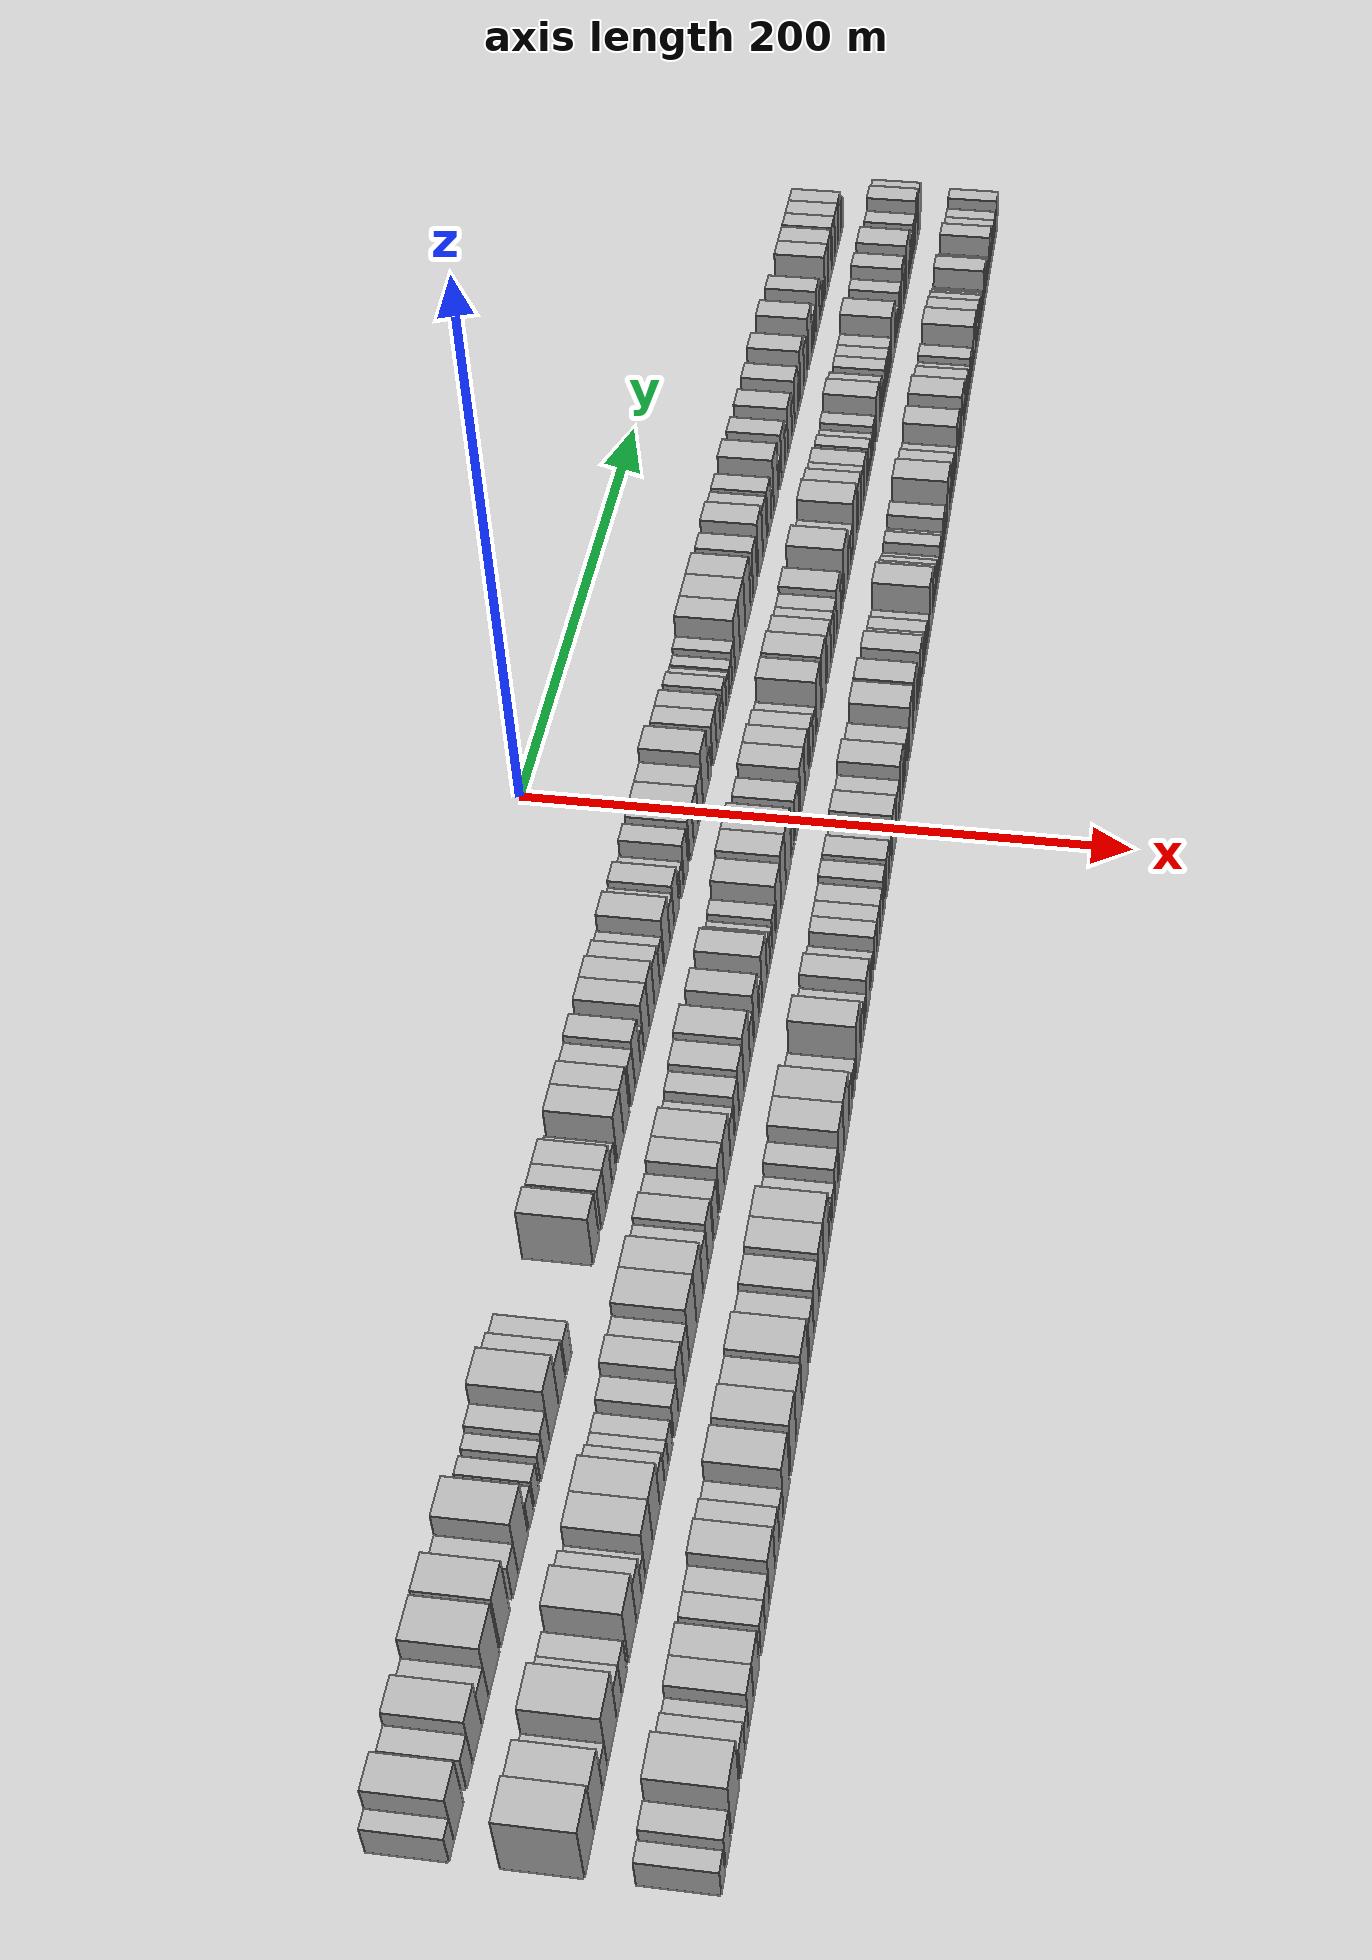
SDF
<sdf version="1.6">
 <world name="default">
  <scene>
   <sky><clouds><speed>12</speed></clouds></sky>
   <ambient>0.4 0.4 0.4 1</ambient>
   <background>0.7 0.7 0.7 1</background>
   <shadows>1</shadows>
  </scene>
  <gravity>0 0 -9.8066</gravity>
  <magnetic_field>6e-06 2.3e-05 -4.2e-05</magnetic_field>
  <physics default="0" name="default_physics" type="ode">
   <ode>
    <solver>
     <type>quick</type>
     <iters>10</iters>
     <sor>1.0</sor>
     <use_dynamic_moi_rescaling>0</use_dynamic_moi_rescaling>
    </solver>
    <constraints>
     <cfm>0</cfm>
     <erp>0.2</erp>
     <contact_max_correcting_vel>100</contact_max_correcting_vel>
     <contact_surface_layer>0.001</contact_surface_layer>
    </constraints>
   </ode>
   <max_step_size>0.004</max_step_size>
   <real_time_factor>1</real_time_factor>
   <real_time_update_rate>250</real_time_update_rate>
  </physics>
  <light name="sun" type="directional">
   <pose>0 0 10 0 0 0</pose>
   <diffuse>0.8 0.8 0.8 1</diffuse>
   <specular>0.2 0.2 0.2 1</specular>
   <attenuation>
    <range>1000</range>
    <constant>0.9</constant>
    <linear>0.01</linear>
    <quadratic>0.001</quadratic>
   </attenuation>
   <direction>-0.5 0.1 -0.9</direction>
  </light>
  <model name="building_1">
   <static>1</static>
   <pose>50.0000 -345.4866 0 0.000000 0.000000 0.000000</pose>
   <link name="link">
    <pose>0 0 6.00 0 0 0</pose>
    <collision name="collision"><geometry><box><size>20.0000 5.0268 12.0000</size></box></geometry></collision>
    <visual name="visual">
     <cast_shadows>0</cast_shadows>
     <geometry><box><size>20.0000 5.0268 12.0000</size></box></geometry>
     <material>
      <script>
       <uri>model://HANNAS_wall/materials/scripts</uri>
       <uri>model://HANNAS_wall/materials/textures</uri>
       <name>vrc/HANNAS_wall</name>
      </script>
     </material>
    </visual>
   </link>
  </model>
  <model name="building_2">
   <static>1</static>
   <pose>50.0000 -338.2310 0 0.000000 0.000000 0.000000</pose>
   <link name="link">
    <pose>0 0 10.50 0 0 0</pose>
    <collision name="collision"><geometry><box><size>20.0000 9.4843 21.0000</size></box></geometry></collision>
    <visual name="visual">
     <cast_shadows>0</cast_shadows>
     <geometry><box><size>20.0000 9.4843 21.0000</size></box></geometry>
     <material>
      <script>
       <uri>model://HANNAS_wall/materials/scripts</uri>
       <uri>model://HANNAS_wall/materials/textures</uri>
       <name>vrc/HANNAS_wall</name>
      </script>
     </material>
    </visual>
   </link>
  </model>
  <model name="building_3">
   <static>1</static>
   <pose>50.0000 -327.2574 0 0.000000 0.000000 0.000000</pose>
   <link name="link">
    <pose>0 0 7.50 0 0 0</pose>
    <collision name="collision"><geometry><box><size>20.0000 6.4630 15.0000</size></box></geometry></collision>
    <visual name="visual">
     <cast_shadows>0</cast_shadows>
     <geometry><box><size>20.0000 6.4630 15.0000</size></box></geometry>
     <material>
      <script>
       <uri>model://HANNAS_wall/materials/scripts</uri>
       <uri>model://HANNAS_wall/materials/textures</uri>
       <name>vrc/HANNAS_wall</name>
      </script>
     </material>
    </visual>
   </link>
  </model>
  <model name="building_4">
   <static>1</static>
   <pose>50.0000 -319.1968 0 0.000000 0.000000 0.000000</pose>
   <link name="link">
    <pose>0 0 10.50 0 0 0</pose>
    <collision name="collision"><geometry><box><size>20.0000 9.6581 21.0000</size></box></geometry></collision>
    <visual name="visual">
     <cast_shadows>0</cast_shadows>
     <geometry><box><size>20.0000 9.6581 21.0000</size></box></geometry>
     <material>
      <script>
       <uri>model://HANNAS_wall/materials/scripts</uri>
       <uri>model://HANNAS_wall/materials/textures</uri>
       <name>vrc/HANNAS_wall</name>
      </script>
     </material>
    </visual>
   </link>
  </model>
  <model name="building_5">
   <static>1</static>
   <pose>50.0000 -310.7020 0 0.000000 0.000000 0.000000</pose>
   <link name="link">
    <pose>0 0 7.50 0 0 0</pose>
    <collision name="collision"><geometry><box><size>20.0000 7.3315 15.0000</size></box></geometry></collision>
    <visual name="visual">
     <cast_shadows>0</cast_shadows>
     <geometry><box><size>20.0000 7.3315 15.0000</size></box></geometry>
     <material>
      <script>
       <uri>model://HANNAS_wall/materials/scripts</uri>
       <uri>model://HANNAS_wall/materials/textures</uri>
       <name>vrc/HANNAS_wall</name>
      </script>
     </material>
    </visual>
   </link>
  </model>
  <model name="building_6">
   <static>1</static>
   <pose>50.0000 -301.1342 0 0.000000 0.000000 0.000000</pose>
   <link name="link">
    <pose>0 0 12.00 0 0 0</pose>
    <collision name="collision"><geometry><box><size>20.0000 11.8042 24.0000</size></box></geometry></collision>
    <visual name="visual">
     <cast_shadows>0</cast_shadows>
     <geometry><box><size>20.0000 11.8042 24.0000</size></box></geometry>
     <material>
      <script>
       <uri>model://HANNAS_wall/materials/scripts</uri>
       <uri>model://HANNAS_wall/materials/textures</uri>
       <name>vrc/HANNAS_wall</name>
      </script>
     </material>
    </visual>
   </link>
  </model>
  <model name="building_7">
   <static>1</static>
   <pose>50.0000 -289.0184 0 0.000000 0.000000 0.000000</pose>
   <link name="link">
    <pose>0 0 12.00 0 0 0</pose>
    <collision name="collision"><geometry><box><size>20.0000 10.4274 24.0000</size></box></geometry></collision>
    <visual name="visual">
     <cast_shadows>0</cast_shadows>
     <geometry><box><size>20.0000 10.4274 24.0000</size></box></geometry>
     <material>
      <script>
       <uri>model://HANNAS_wall/materials/scripts</uri>
       <uri>model://HANNAS_wall/materials/textures</uri>
       <name>vrc/HANNAS_wall</name>
      </script>
     </material>
    </visual>
   </link>
  </model>
  <model name="building_8">
   <static>1</static>
   <pose>50.0000 -277.3767 0 0.000000 0.000000 0.000000</pose>
   <link name="link">
    <pose>0 0 7.50 0 0 0</pose>
    <collision name="collision"><geometry><box><size>20.0000 6.8560 15.0000</size></box></geometry></collision>
    <visual name="visual">
     <cast_shadows>0</cast_shadows>
     <geometry><box><size>20.0000 6.8560 15.0000</size></box></geometry>
     <material>
      <script>
       <uri>model://HANNAS_wall/materials/scripts</uri>
       <uri>model://HANNAS_wall/materials/textures</uri>
       <name>vrc/HANNAS_wall</name>
      </script>
     </material>
    </visual>
   </link>
  </model>
  <model name="building_9">
   <static>1</static>
   <pose>50.0000 -268.2881 0 0.000000 0.000000 0.000000</pose>
   <link name="link">
    <pose>0 0 12.00 0 0 0</pose>
    <collision name="collision"><geometry><box><size>20.0000 11.3212 24.0000</size></box></geometry></collision>
    <visual name="visual">
     <cast_shadows>0</cast_shadows>
     <geometry><box><size>20.0000 11.3212 24.0000</size></box></geometry>
     <material>
      <script>
       <uri>model://HANNAS_wall/materials/scripts</uri>
       <uri>model://HANNAS_wall/materials/textures</uri>
       <name>vrc/HANNAS_wall</name>
      </script>
     </material>
    </visual>
   </link>
  </model>
  <model name="building_10">
   <static>1</static>
   <pose>50.0000 -258.7384 0 0.000000 0.000000 0.000000</pose>
   <link name="link">
    <pose>0 0 6.00 0 0 0</pose>
    <collision name="collision"><geometry><box><size>20.0000 5.7780 12.0000</size></box></geometry></collision>
    <visual name="visual">
     <cast_shadows>0</cast_shadows>
     <geometry><box><size>20.0000 5.7780 12.0000</size></box></geometry>
     <material>
      <script>
       <uri>model://HANNAS_wall/materials/scripts</uri>
       <uri>model://HANNAS_wall/materials/textures</uri>
       <name>vrc/HANNAS_wall</name>
      </script>
     </material>
    </visual>
   </link>
  </model>
  <model name="building_11">
   <static>1</static>
   <pose>50.0000 -252.1770 0 0.000000 0.000000 0.000000</pose>
   <link name="link">
    <pose>0 0 6.00 0 0 0</pose>
    <collision name="collision"><geometry><box><size>20.0000 5.3448 12.0000</size></box></geometry></collision>
    <visual name="visual">
     <cast_shadows>0</cast_shadows>
     <geometry><box><size>20.0000 5.3448 12.0000</size></box></geometry>
     <material>
      <script>
       <uri>model://HANNAS_wall/materials/scripts</uri>
       <uri>model://HANNAS_wall/materials/textures</uri>
       <name>vrc/HANNAS_wall</name>
      </script>
     </material>
    </visual>
   </link>
  </model>
  <model name="building_12">
   <static>1</static>
   <pose>50.0000 -245.0418 0 0.000000 0.000000 0.000000</pose>
   <link name="link">
    <pose>0 0 6.00 0 0 0</pose>
    <collision name="collision"><geometry><box><size>20.0000 4.9258 12.0000</size></box></geometry></collision>
    <visual name="visual">
     <cast_shadows>0</cast_shadows>
     <geometry><box><size>20.0000 4.9258 12.0000</size></box></geometry>
     <material>
      <script>
       <uri>model://HANNAS_wall/materials/scripts</uri>
       <uri>model://HANNAS_wall/materials/textures</uri>
       <name>vrc/HANNAS_wall</name>
      </script>
     </material>
    </visual>
   </link>
  </model>
  <model name="building_13">
   <static>1</static>
   <pose>50.0000 -239.1823 0 0.000000 0.000000 0.000000</pose>
   <link name="link">
    <pose>0 0 7.50 0 0 0</pose>
    <collision name="collision"><geometry><box><size>20.0000 6.7931 15.0000</size></box></geometry></collision>
    <visual name="visual">
     <cast_shadows>0</cast_shadows>
     <geometry><box><size>20.0000 6.7931 15.0000</size></box></geometry>
     <material>
      <script>
       <uri>model://HANNAS_wall/materials/scripts</uri>
       <uri>model://HANNAS_wall/materials/textures</uri>
       <name>vrc/HANNAS_wall</name>
      </script>
     </material>
    </visual>
   </link>
  </model>
  <model name="building_14">
   <static>1</static>
   <pose>50.0000 -230.1749 0 0.000000 0.000000 0.000000</pose>
   <link name="link">
    <pose>0 0 12.00 0 0 0</pose>
    <collision name="collision"><geometry><box><size>20.0000 11.2219 24.0000</size></box></geometry></collision>
    <visual name="visual">
     <cast_shadows>0</cast_shadows>
     <geometry><box><size>20.0000 11.2219 24.0000</size></box></geometry>
     <material>
      <script>
       <uri>model://HANNAS_wall/materials/scripts</uri>
       <uri>model://HANNAS_wall/materials/textures</uri>
       <name>vrc/HANNAS_wall</name>
      </script>
     </material>
    </visual>
   </link>
  </model>
  <model name="building_15">
   <static>1</static>
   <pose>50.0000 -220.2585 0 0.000000 0.000000 0.000000</pose>
   <link name="link">
    <pose>0 0 9.00 0 0 0</pose>
    <collision name="collision"><geometry><box><size>20.0000 8.6108 18.0000</size></box></geometry></collision>
    <visual name="visual">
     <cast_shadows>0</cast_shadows>
     <geometry><box><size>20.0000 8.6108 18.0000</size></box></geometry>
     <material>
      <script>
       <uri>model://HANNAS_wall/materials/scripts</uri>
       <uri>model://HANNAS_wall/materials/textures</uri>
       <name>vrc/HANNAS_wall</name>
      </script>
     </material>
    </visual>
   </link>
  </model>
  <model name="building_16">
   <static>1</static>
   <pose>50.0000 -211.4764 0 0.000000 0.000000 0.000000</pose>
   <link name="link">
    <pose>0 0 7.50 0 0 0</pose>
    <collision name="collision"><geometry><box><size>20.0000 6.9535 15.0000</size></box></geometry></collision>
    <visual name="visual">
     <cast_shadows>0</cast_shadows>
     <geometry><box><size>20.0000 6.9535 15.0000</size></box></geometry>
     <material>
      <script>
       <uri>model://HANNAS_wall/materials/scripts</uri>
       <uri>model://HANNAS_wall/materials/textures</uri>
       <name>vrc/HANNAS_wall</name>
      </script>
     </material>
    </visual>
   </link>
  </model>
  <model name="building_17">
   <static>1</static>
   <pose>50.0000 -174.6154 0 0.000000 0.000000 0.000000</pose>
   <link name="link">
    <pose>0 0 10.50 0 0 0</pose>
    <collision name="collision"><geometry><box><size>20.0000 8.9228 21.0000</size></box></geometry></collision>
    <visual name="visual">
     <cast_shadows>0</cast_shadows>
     <geometry><box><size>20.0000 8.9228 21.0000</size></box></geometry>
     <material>
      <script>
       <uri>model://HANNAS_wall/materials/scripts</uri>
       <uri>model://HANNAS_wall/materials/textures</uri>
       <name>vrc/HANNAS_wall</name>
      </script>
     </material>
    </visual>
   </link>
  </model>
  <model name="building_18">
   <static>1</static>
   <pose>50.0000 -163.4706 0 0.000000 0.000000 0.000000</pose>
   <link name="link">
    <pose>0 0 9.00 0 0 0</pose>
    <collision name="collision"><geometry><box><size>20.0000 7.3669 18.0000</size></box></geometry></collision>
    <visual name="visual">
     <cast_shadows>0</cast_shadows>
     <geometry><box><size>20.0000 7.3669 18.0000</size></box></geometry>
     <material>
      <script>
       <uri>model://HANNAS_wall/materials/scripts</uri>
       <uri>model://HANNAS_wall/materials/textures</uri>
       <name>vrc/HANNAS_wall</name>
      </script>
     </material>
    </visual>
   </link>
  </model>
  <model name="building_19">
   <static>1</static>
   <pose>50.0000 -155.4612 0 0.000000 0.000000 0.000000</pose>
   <link name="link">
    <pose>0 0 9.00 0 0 0</pose>
    <collision name="collision"><geometry><box><size>20.0000 8.6519 18.0000</size></box></geometry></collision>
    <visual name="visual">
     <cast_shadows>0</cast_shadows>
     <geometry><box><size>20.0000 8.6519 18.0000</size></box></geometry>
     <material>
      <script>
       <uri>model://HANNAS_wall/materials/scripts</uri>
       <uri>model://HANNAS_wall/materials/textures</uri>
       <name>vrc/HANNAS_wall</name>
      </script>
     </material>
    </visual>
   </link>
  </model>
  <model name="building_20">
   <static>1</static>
   <pose>50.0000 -148.3077 0 0.000000 0.000000 0.000000</pose>
   <link name="link">
    <pose>0 0 6.00 0 0 0</pose>
    <collision name="collision"><geometry><box><size>20.0000 5.6550 12.0000</size></box></geometry></collision>
    <visual name="visual">
     <cast_shadows>0</cast_shadows>
     <geometry><box><size>20.0000 5.6550 12.0000</size></box></geometry>
     <material>
      <script>
       <uri>model://HANNAS_wall/materials/scripts</uri>
       <uri>model://HANNAS_wall/materials/textures</uri>
       <name>vrc/HANNAS_wall</name>
      </script>
     </material>
    </visual>
   </link>
  </model>
  <model name="building_21">
   <static>1</static>
   <pose>50.0000 -138.5372 0 0.000000 0.000000 0.000000</pose>
   <link name="link">
    <pose>0 0 10.50 0 0 0</pose>
    <collision name="collision"><geometry><box><size>20.0000 9.8859 21.0000</size></box></geometry></collision>
    <visual name="visual">
     <cast_shadows>0</cast_shadows>
     <geometry><box><size>20.0000 9.8859 21.0000</size></box></geometry>
     <material>
      <script>
       <uri>model://HANNAS_wall/materials/scripts</uri>
       <uri>model://HANNAS_wall/materials/textures</uri>
       <name>vrc/HANNAS_wall</name>
      </script>
     </material>
    </visual>
   </link>
  </model>
  <model name="building_22">
   <static>1</static>
   <pose>50.0000 -129.3131 0 0.000000 0.000000 0.000000</pose>
   <link name="link">
    <pose>0 0 10.50 0 0 0</pose>
    <collision name="collision"><geometry><box><size>20.0000 8.5625 21.0000</size></box></geometry></collision>
    <visual name="visual">
     <cast_shadows>0</cast_shadows>
     <geometry><box><size>20.0000 8.5625 21.0000</size></box></geometry>
     <material>
      <script>
       <uri>model://HANNAS_wall/materials/scripts</uri>
       <uri>model://HANNAS_wall/materials/textures</uri>
       <name>vrc/HANNAS_wall</name>
      </script>
     </material>
    </visual>
   </link>
  </model>
  <model name="building_23">
   <static>1</static>
   <pose>50.0000 -119.3993 0 0.000000 0.000000 0.000000</pose>
   <link name="link">
    <pose>0 0 9.00 0 0 0</pose>
    <collision name="collision"><geometry><box><size>20.0000 7.2651 18.0000</size></box></geometry></collision>
    <visual name="visual">
     <cast_shadows>0</cast_shadows>
     <geometry><box><size>20.0000 7.2651 18.0000</size></box></geometry>
     <material>
      <script>
       <uri>model://HANNAS_wall/materials/scripts</uri>
       <uri>model://HANNAS_wall/materials/textures</uri>
       <name>vrc/HANNAS_wall</name>
      </script>
     </material>
    </visual>
   </link>
  </model>
  <model name="building_24">
   <static>1</static>
   <pose>50.0000 -111.4311 0 0.000000 0.000000 0.000000</pose>
   <link name="link">
    <pose>0 0 10.50 0 0 0</pose>
    <collision name="collision"><geometry><box><size>20.0000 8.6713 21.0000</size></box></geometry></collision>
    <visual name="visual">
     <cast_shadows>0</cast_shadows>
     <geometry><box><size>20.0000 8.6713 21.0000</size></box></geometry>
     <material>
      <script>
       <uri>model://HANNAS_wall/materials/scripts</uri>
       <uri>model://HANNAS_wall/materials/textures</uri>
       <name>vrc/HANNAS_wall</name>
      </script>
     </material>
    </visual>
   </link>
  </model>
  <model name="building_25">
   <static>1</static>
   <pose>50.0000 -104.4094 0 0.000000 0.000000 0.000000</pose>
   <link name="link">
    <pose>0 0 6.00 0 0 0</pose>
    <collision name="collision"><geometry><box><size>20.0000 5.3721 12.0000</size></box></geometry></collision>
    <visual name="visual">
     <cast_shadows>0</cast_shadows>
     <geometry><box><size>20.0000 5.3721 12.0000</size></box></geometry>
     <material>
      <script>
       <uri>model://HANNAS_wall/materials/scripts</uri>
       <uri>model://HANNAS_wall/materials/textures</uri>
       <name>vrc/HANNAS_wall</name>
      </script>
     </material>
    </visual>
   </link>
  </model>
  <model name="building_26">
   <static>1</static>
   <pose>50.0000 -97.2492 0 0.000000 0.000000 0.000000</pose>
   <link name="link">
    <pose>0 0 10.50 0 0 0</pose>
    <collision name="collision"><geometry><box><size>20.0000 8.9485 21.0000</size></box></geometry></collision>
    <visual name="visual">
     <cast_shadows>0</cast_shadows>
     <geometry><box><size>20.0000 8.9485 21.0000</size></box></geometry>
     <material>
      <script>
       <uri>model://HANNAS_wall/materials/scripts</uri>
       <uri>model://HANNAS_wall/materials/textures</uri>
       <name>vrc/HANNAS_wall</name>
      </script>
     </material>
    </visual>
   </link>
  </model>
  <model name="building_27">
   <static>1</static>
   <pose>50.0000 -88.4928 0 0.000000 0.000000 0.000000</pose>
   <link name="link">
    <pose>0 0 10.50 0 0 0</pose>
    <collision name="collision"><geometry><box><size>20.0000 8.5643 21.0000</size></box></geometry></collision>
    <visual name="visual">
     <cast_shadows>0</cast_shadows>
     <geometry><box><size>20.0000 8.5643 21.0000</size></box></geometry>
     <material>
      <script>
       <uri>model://HANNAS_wall/materials/scripts</uri>
       <uri>model://HANNAS_wall/materials/textures</uri>
       <name>vrc/HANNAS_wall</name>
      </script>
     </material>
    </visual>
   </link>
  </model>
  <model name="building_28">
   <static>1</static>
   <pose>50.0000 -79.7274 0 0.000000 0.000000 0.000000</pose>
   <link name="link">
    <pose>0 0 9.00 0 0 0</pose>
    <collision name="collision"><geometry><box><size>20.0000 8.9664 18.0000</size></box></geometry></collision>
    <visual name="visual">
     <cast_shadows>0</cast_shadows>
     <geometry><box><size>20.0000 8.9664 18.0000</size></box></geometry>
     <material>
      <script>
       <uri>model://HANNAS_wall/materials/scripts</uri>
       <uri>model://HANNAS_wall/materials/textures</uri>
       <name>vrc/HANNAS_wall</name>
      </script>
     </material>
    </visual>
   </link>
  </model>
  <model name="building_29">
   <static>1</static>
   <pose>50.0000 -72.0207 0 0.000000 0.000000 0.000000</pose>
   <link name="link">
    <pose>0 0 7.50 0 0 0</pose>
    <collision name="collision"><geometry><box><size>20.0000 6.4469 15.0000</size></box></geometry></collision>
    <visual name="visual">
     <cast_shadows>0</cast_shadows>
     <geometry><box><size>20.0000 6.4469 15.0000</size></box></geometry>
     <material>
      <script>
       <uri>model://HANNAS_wall/materials/scripts</uri>
       <uri>model://HANNAS_wall/materials/textures</uri>
       <name>vrc/HANNAS_wall</name>
      </script>
     </material>
    </visual>
   </link>
  </model>
  <model name="building_30">
   <static>1</static>
   <pose>50.0000 -62.7804 0 0.000000 0.000000 0.000000</pose>
   <link name="link">
    <pose>0 0 10.50 0 0 0</pose>
    <collision name="collision"><geometry><box><size>20.0000 10.0338 21.0000</size></box></geometry></collision>
    <visual name="visual">
     <cast_shadows>0</cast_shadows>
     <geometry><box><size>20.0000 10.0338 21.0000</size></box></geometry>
     <material>
      <script>
       <uri>model://HANNAS_wall/materials/scripts</uri>
       <uri>model://HANNAS_wall/materials/textures</uri>
       <name>vrc/HANNAS_wall</name>
      </script>
     </material>
    </visual>
   </link>
  </model>
  <model name="building_31">
   <static>1</static>
   <pose>50.0000 -54.1605 0 0.000000 0.000000 0.000000</pose>
   <link name="link">
    <pose>0 0 7.50 0 0 0</pose>
    <collision name="collision"><geometry><box><size>20.0000 7.2061 15.0000</size></box></geometry></collision>
    <visual name="visual">
     <cast_shadows>0</cast_shadows>
     <geometry><box><size>20.0000 7.2061 15.0000</size></box></geometry>
     <material>
      <script>
       <uri>model://HANNAS_wall/materials/scripts</uri>
       <uri>model://HANNAS_wall/materials/textures</uri>
       <name>vrc/HANNAS_wall</name>
      </script>
     </material>
    </visual>
   </link>
  </model>
  <model name="building_32">
   <static>1</static>
   <pose>50.0000 -46.3682 0 0.000000 0.000000 0.000000</pose>
   <link name="link">
    <pose>0 0 9.00 0 0 0</pose>
    <collision name="collision"><geometry><box><size>20.0000 8.3784 18.0000</size></box></geometry></collision>
    <visual name="visual">
     <cast_shadows>0</cast_shadows>
     <geometry><box><size>20.0000 8.3784 18.0000</size></box></geometry>
     <material>
      <script>
       <uri>model://HANNAS_wall/materials/scripts</uri>
       <uri>model://HANNAS_wall/materials/textures</uri>
       <name>vrc/HANNAS_wall</name>
      </script>
     </material>
    </visual>
   </link>
  </model>
  <model name="building_33">
   <static>1</static>
   <pose>50.0000 -36.5530 0 0.000000 0.000000 0.000000</pose>
   <link name="link">
    <pose>0 0 6.00 0 0 0</pose>
    <collision name="collision"><geometry><box><size>20.0000 5.2521 12.0000</size></box></geometry></collision>
    <visual name="visual">
     <cast_shadows>0</cast_shadows>
     <geometry><box><size>20.0000 5.2521 12.0000</size></box></geometry>
     <material>
      <script>
       <uri>model://HANNAS_wall/materials/scripts</uri>
       <uri>model://HANNAS_wall/materials/textures</uri>
       <name>vrc/HANNAS_wall</name>
      </script>
     </material>
    </visual>
   </link>
  </model>
  <model name="building_34">
   <static>1</static>
   <pose>50.0000 -29.1841 0 0.000000 0.000000 0.000000</pose>
   <link name="link">
    <pose>0 0 9.00 0 0 0</pose>
    <collision name="collision"><geometry><box><size>20.0000 7.4859 18.0000</size></box></geometry></collision>
    <visual name="visual">
     <cast_shadows>0</cast_shadows>
     <geometry><box><size>20.0000 7.4859 18.0000</size></box></geometry>
     <material>
      <script>
       <uri>model://HANNAS_wall/materials/scripts</uri>
       <uri>model://HANNAS_wall/materials/textures</uri>
       <name>vrc/HANNAS_wall</name>
      </script>
     </material>
    </visual>
   </link>
  </model>
  <model name="building_35">
   <static>1</static>
   <pose>50.0000 -18.7066 0 0.000000 0.000000 0.000000</pose>
   <link name="link">
    <pose>0 0 9.00 0 0 0</pose>
    <collision name="collision"><geometry><box><size>20.0000 7.4691 18.0000</size></box></geometry></collision>
    <visual name="visual">
     <cast_shadows>0</cast_shadows>
     <geometry><box><size>20.0000 7.4691 18.0000</size></box></geometry>
     <material>
      <script>
       <uri>model://HANNAS_wall/materials/scripts</uri>
       <uri>model://HANNAS_wall/materials/textures</uri>
       <name>vrc/HANNAS_wall</name>
      </script>
     </material>
    </visual>
   </link>
  </model>
  <model name="building_36">
   <static>1</static>
   <pose>50.0000 -10.5973 0 0.000000 0.000000 0.000000</pose>
   <link name="link">
    <pose>0 0 9.00 0 0 0</pose>
    <collision name="collision"><geometry><box><size>20.0000 8.7495 18.0000</size></box></geometry></collision>
    <visual name="visual">
     <cast_shadows>0</cast_shadows>
     <geometry><box><size>20.0000 8.7495 18.0000</size></box></geometry>
     <material>
      <script>
       <uri>model://HANNAS_wall/materials/scripts</uri>
       <uri>model://HANNAS_wall/materials/textures</uri>
       <name>vrc/HANNAS_wall</name>
      </script>
     </material>
    </visual>
   </link>
  </model>
  <model name="building_37">
   <static>1</static>
   <pose>50.0000 -1.7808 0 0.000000 0.000000 0.000000</pose>
   <link name="link">
    <pose>0 0 9.00 0 0 0</pose>
    <collision name="collision"><geometry><box><size>20.0000 8.8835 18.0000</size></box></geometry></collision>
    <visual name="visual">
     <cast_shadows>0</cast_shadows>
     <geometry><box><size>20.0000 8.8835 18.0000</size></box></geometry>
     <material>
      <script>
       <uri>model://HANNAS_wall/materials/scripts</uri>
       <uri>model://HANNAS_wall/materials/textures</uri>
       <name>vrc/HANNAS_wall</name>
      </script>
     </material>
    </visual>
   </link>
  </model>
  <model name="building_38">
   <static>1</static>
   <pose>50.0000 8.0805 0 0.000000 0.000000 0.000000</pose>
   <link name="link">
    <pose>0 0 12.00 0 0 0</pose>
    <collision name="collision"><geometry><box><size>20.0000 10.8393 24.0000</size></box></geometry></collision>
    <visual name="visual">
     <cast_shadows>0</cast_shadows>
     <geometry><box><size>20.0000 10.8393 24.0000</size></box></geometry>
     <material>
      <script>
       <uri>model://HANNAS_wall/materials/scripts</uri>
       <uri>model://HANNAS_wall/materials/textures</uri>
       <name>vrc/HANNAS_wall</name>
      </script>
     </material>
    </visual>
   </link>
  </model>
  <model name="building_39">
   <static>1</static>
   <pose>50.0000 16.0215 0 0.000000 0.000000 0.000000</pose>
   <link name="link">
    <pose>0 0 6.00 0 0 0</pose>
    <collision name="collision"><geometry><box><size>20.0000 5.0427 12.0000</size></box></geometry></collision>
    <visual name="visual">
     <cast_shadows>0</cast_shadows>
     <geometry><box><size>20.0000 5.0427 12.0000</size></box></geometry>
     <material>
      <script>
       <uri>model://HANNAS_wall/materials/scripts</uri>
       <uri>model://HANNAS_wall/materials/textures</uri>
       <name>vrc/HANNAS_wall</name>
      </script>
     </material>
    </visual>
   </link>
  </model>
  <model name="building_40">
   <static>1</static>
   <pose>50.0000 25.6742 0 0.000000 0.000000 0.000000</pose>
   <link name="link">
    <pose>0 0 9.00 0 0 0</pose>
    <collision name="collision"><geometry><box><size>20.0000 8.2626 18.0000</size></box></geometry></collision>
    <visual name="visual">
     <cast_shadows>0</cast_shadows>
     <geometry><box><size>20.0000 8.2626 18.0000</size></box></geometry>
     <material>
      <script>
       <uri>model://HANNAS_wall/materials/scripts</uri>
       <uri>model://HANNAS_wall/materials/textures</uri>
       <name>vrc/HANNAS_wall</name>
      </script>
     </material>
    </visual>
   </link>
  </model>
  <model name="building_41">
   <static>1</static>
   <pose>50.0000 33.6685 0 0.000000 0.000000 0.000000</pose>
   <link name="link">
    <pose>0 0 9.00 0 0 0</pose>
    <collision name="collision"><geometry><box><size>20.0000 7.7261 18.0000</size></box></geometry></collision>
    <visual name="visual">
     <cast_shadows>0</cast_shadows>
     <geometry><box><size>20.0000 7.7261 18.0000</size></box></geometry>
     <material>
      <script>
       <uri>model://HANNAS_wall/materials/scripts</uri>
       <uri>model://HANNAS_wall/materials/textures</uri>
       <name>vrc/HANNAS_wall</name>
      </script>
     </material>
    </visual>
   </link>
  </model>
  <model name="building_42">
   <static>1</static>
   <pose>50.0000 40.3469 0 0.000000 0.000000 0.000000</pose>
   <link name="link">
    <pose>0 0 6.00 0 0 0</pose>
    <collision name="collision"><geometry><box><size>20.0000 5.6309 12.0000</size></box></geometry></collision>
    <visual name="visual">
     <cast_shadows>0</cast_shadows>
     <geometry><box><size>20.0000 5.6309 12.0000</size></box></geometry>
     <material>
      <script>
       <uri>model://HANNAS_wall/materials/scripts</uri>
       <uri>model://HANNAS_wall/materials/textures</uri>
       <name>vrc/HANNAS_wall</name>
      </script>
     </material>
    </visual>
   </link>
  </model>
  <model name="building_43">
   <static>1</static>
   <pose>50.0000 46.4222 0 0.000000 0.000000 0.000000</pose>
   <link name="link">
    <pose>0 0 7.50 0 0 0</pose>
    <collision name="collision"><geometry><box><size>20.0000 6.5196 15.0000</size></box></geometry></collision>
    <visual name="visual">
     <cast_shadows>0</cast_shadows>
     <geometry><box><size>20.0000 6.5196 15.0000</size></box></geometry>
     <material>
      <script>
       <uri>model://HANNAS_wall/materials/scripts</uri>
       <uri>model://HANNAS_wall/materials/textures</uri>
       <name>vrc/HANNAS_wall</name>
      </script>
     </material>
    </visual>
   </link>
  </model>
  <model name="building_44">
   <static>1</static>
   <pose>50.0000 52.6147 0 0.000000 0.000000 0.000000</pose>
   <link name="link">
    <pose>0 0 6.00 0 0 0</pose>
    <collision name="collision"><geometry><box><size>20.0000 5.8656 12.0000</size></box></geometry></collision>
    <visual name="visual">
     <cast_shadows>0</cast_shadows>
     <geometry><box><size>20.0000 5.8656 12.0000</size></box></geometry>
     <material>
      <script>
       <uri>model://HANNAS_wall/materials/scripts</uri>
       <uri>model://HANNAS_wall/materials/textures</uri>
       <name>vrc/HANNAS_wall</name>
      </script>
     </material>
    </visual>
   </link>
  </model>
  <model name="building_45">
   <static>1</static>
   <pose>50.0000 59.1425 0 0.000000 0.000000 0.000000</pose>
   <link name="link">
    <pose>0 0 6.00 0 0 0</pose>
    <collision name="collision"><geometry><box><size>20.0000 5.1899 12.0000</size></box></geometry></collision>
    <visual name="visual">
     <cast_shadows>0</cast_shadows>
     <geometry><box><size>20.0000 5.1899 12.0000</size></box></geometry>
     <material>
      <script>
       <uri>model://HANNAS_wall/materials/scripts</uri>
       <uri>model://HANNAS_wall/materials/textures</uri>
       <name>vrc/HANNAS_wall</name>
      </script>
     </material>
    </visual>
   </link>
  </model>
  <model name="building_46">
   <static>1</static>
   <pose>50.0000 64.8437 0 0.000000 0.000000 0.000000</pose>
   <link name="link">
    <pose>0 0 7.50 0 0 0</pose>
    <collision name="collision"><geometry><box><size>20.0000 6.2126 15.0000</size></box></geometry></collision>
    <visual name="visual">
     <cast_shadows>0</cast_shadows>
     <geometry><box><size>20.0000 6.2126 15.0000</size></box></geometry>
     <material>
      <script>
       <uri>model://HANNAS_wall/materials/scripts</uri>
       <uri>model://HANNAS_wall/materials/textures</uri>
       <name>vrc/HANNAS_wall</name>
      </script>
     </material>
    </visual>
   </link>
  </model>
  <model name="building_47">
   <static>1</static>
   <pose>50.0000 73.2977 0 0.000000 0.000000 0.000000</pose>
   <link name="link">
    <pose>0 0 12.00 0 0 0</pose>
    <collision name="collision"><geometry><box><size>20.0000 10.6954 24.0000</size></box></geometry></collision>
    <visual name="visual">
     <cast_shadows>0</cast_shadows>
     <geometry><box><size>20.0000 10.6954 24.0000</size></box></geometry>
     <material>
      <script>
       <uri>model://HANNAS_wall/materials/scripts</uri>
       <uri>model://HANNAS_wall/materials/textures</uri>
       <name>vrc/HANNAS_wall</name>
      </script>
     </material>
    </visual>
   </link>
  </model>
  <model name="building_48">
   <static>1</static>
   <pose>50.0000 84.5868 0 0.000000 0.000000 0.000000</pose>
   <link name="link">
    <pose>0 0 12.00 0 0 0</pose>
    <collision name="collision"><geometry><box><size>20.0000 11.8827 24.0000</size></box></geometry></collision>
    <visual name="visual">
     <cast_shadows>0</cast_shadows>
     <geometry><box><size>20.0000 11.8827 24.0000</size></box></geometry>
     <material>
      <script>
       <uri>model://HANNAS_wall/materials/scripts</uri>
       <uri>model://HANNAS_wall/materials/textures</uri>
       <name>vrc/HANNAS_wall</name>
      </script>
     </material>
    </visual>
   </link>
  </model>
  <model name="building_49">
   <static>1</static>
   <pose>50.0000 96.2651 0 0.000000 0.000000 0.000000</pose>
   <link name="link">
    <pose>0 0 12.00 0 0 0</pose>
    <collision name="collision"><geometry><box><size>20.0000 11.4740 24.0000</size></box></geometry></collision>
    <visual name="visual">
     <cast_shadows>0</cast_shadows>
     <geometry><box><size>20.0000 11.4740 24.0000</size></box></geometry>
     <material>
      <script>
       <uri>model://HANNAS_wall/materials/scripts</uri>
       <uri>model://HANNAS_wall/materials/textures</uri>
       <name>vrc/HANNAS_wall</name>
      </script>
     </material>
    </visual>
   </link>
  </model>
  <model name="building_50">
   <static>1</static>
   <pose>50.0000 105.0200 0 0.000000 0.000000 0.000000</pose>
   <link name="link">
    <pose>0 0 7.50 0 0 0</pose>
    <collision name="collision"><geometry><box><size>20.0000 6.0358 15.0000</size></box></geometry></collision>
    <visual name="visual">
     <cast_shadows>0</cast_shadows>
     <geometry><box><size>20.0000 6.0358 15.0000</size></box></geometry>
     <material>
      <script>
       <uri>model://HANNAS_wall/materials/scripts</uri>
       <uri>model://HANNAS_wall/materials/textures</uri>
       <name>vrc/HANNAS_wall</name>
      </script>
     </material>
    </visual>
   </link>
  </model>
  <model name="building_51">
   <static>1</static>
   <pose>50.0000 112.4565 0 0.000000 0.000000 0.000000</pose>
   <link name="link">
    <pose>0 0 10.50 0 0 0</pose>
    <collision name="collision"><geometry><box><size>20.0000 8.8372 21.0000</size></box></geometry></collision>
    <visual name="visual">
     <cast_shadows>0</cast_shadows>
     <geometry><box><size>20.0000 8.8372 21.0000</size></box></geometry>
     <material>
      <script>
       <uri>model://HANNAS_wall/materials/scripts</uri>
       <uri>model://HANNAS_wall/materials/textures</uri>
       <name>vrc/HANNAS_wall</name>
      </script>
     </material>
    </visual>
   </link>
  </model>
  <model name="building_52">
   <static>1</static>
   <pose>50.0000 125.2508 0 0.000000 0.000000 0.000000</pose>
   <link name="link">
    <pose>0 0 12.00 0 0 0</pose>
    <collision name="collision"><geometry><box><size>20.0000 10.7513 24.0000</size></box></geometry></collision>
    <visual name="visual">
     <cast_shadows>0</cast_shadows>
     <geometry><box><size>20.0000 10.7513 24.0000</size></box></geometry>
     <material>
      <script>
       <uri>model://HANNAS_wall/materials/scripts</uri>
       <uri>model://HANNAS_wall/materials/textures</uri>
       <name>vrc/HANNAS_wall</name>
      </script>
     </material>
    </visual>
   </link>
  </model>
  <model name="building_53">
   <static>1</static>
   <pose>50.0000 135.3227 0 0.000000 0.000000 0.000000</pose>
   <link name="link">
    <pose>0 0 10.50 0 0 0</pose>
    <collision name="collision"><geometry><box><size>20.0000 9.3926 21.0000</size></box></geometry></collision>
    <visual name="visual">
     <cast_shadows>0</cast_shadows>
     <geometry><box><size>20.0000 9.3926 21.0000</size></box></geometry>
     <material>
      <script>
       <uri>model://HANNAS_wall/materials/scripts</uri>
       <uri>model://HANNAS_wall/materials/textures</uri>
       <name>vrc/HANNAS_wall</name>
      </script>
     </material>
    </visual>
   </link>
  </model>
  <model name="building_54">
   <static>1</static>
   <pose>50.0000 146.4095 0 0.000000 0.000000 0.000000</pose>
   <link name="link">
    <pose>0 0 10.50 0 0 0</pose>
    <collision name="collision"><geometry><box><size>20.0000 8.7809 21.0000</size></box></geometry></collision>
    <visual name="visual">
     <cast_shadows>0</cast_shadows>
     <geometry><box><size>20.0000 8.7809 21.0000</size></box></geometry>
     <material>
      <script>
       <uri>model://HANNAS_wall/materials/scripts</uri>
       <uri>model://HANNAS_wall/materials/textures</uri>
       <name>vrc/HANNAS_wall</name>
      </script>
     </material>
    </visual>
   </link>
  </model>
  <model name="building_55">
   <static>1</static>
   <pose>50.0000 153.7830 0 0.000000 0.000000 0.000000</pose>
   <link name="link">
    <pose>0 0 6.00 0 0 0</pose>
    <collision name="collision"><geometry><box><size>20.0000 5.9661 12.0000</size></box></geometry></collision>
    <visual name="visual">
     <cast_shadows>0</cast_shadows>
     <geometry><box><size>20.0000 5.9661 12.0000</size></box></geometry>
     <material>
      <script>
       <uri>model://HANNAS_wall/materials/scripts</uri>
       <uri>model://HANNAS_wall/materials/textures</uri>
       <name>vrc/HANNAS_wall</name>
      </script>
     </material>
    </visual>
   </link>
  </model>
  <model name="building_56">
   <static>1</static>
   <pose>50.0000 162.0138 0 0.000000 0.000000 0.000000</pose>
   <link name="link">
    <pose>0 0 12.00 0 0 0</pose>
    <collision name="collision"><geometry><box><size>20.0000 10.4956 24.0000</size></box></geometry></collision>
    <visual name="visual">
     <cast_shadows>0</cast_shadows>
     <geometry><box><size>20.0000 10.4956 24.0000</size></box></geometry>
     <material>
      <script>
       <uri>model://HANNAS_wall/materials/scripts</uri>
       <uri>model://HANNAS_wall/materials/textures</uri>
       <name>vrc/HANNAS_wall</name>
      </script>
     </material>
    </visual>
   </link>
  </model>
  <model name="building_57">
   <static>1</static>
   <pose>50.0000 173.0753 0 0.000000 0.000000 0.000000</pose>
   <link name="link">
    <pose>0 0 6.00 0 0 0</pose>
    <collision name="collision"><geometry><box><size>20.0000 5.6274 12.0000</size></box></geometry></collision>
    <visual name="visual">
     <cast_shadows>0</cast_shadows>
     <geometry><box><size>20.0000 5.6274 12.0000</size></box></geometry>
     <material>
      <script>
       <uri>model://HANNAS_wall/materials/scripts</uri>
       <uri>model://HANNAS_wall/materials/textures</uri>
       <name>vrc/HANNAS_wall</name>
      </script>
     </material>
    </visual>
   </link>
  </model>
  <model name="building_58">
   <static>1</static>
   <pose>50.0000 180.4229 0 0.000000 0.000000 0.000000</pose>
   <link name="link">
    <pose>0 0 10.50 0 0 0</pose>
    <collision name="collision"><geometry><box><size>20.0000 9.0678 21.0000</size></box></geometry></collision>
    <visual name="visual">
     <cast_shadows>0</cast_shadows>
     <geometry><box><size>20.0000 9.0678 21.0000</size></box></geometry>
     <material>
      <script>
       <uri>model://HANNAS_wall/materials/scripts</uri>
       <uri>model://HANNAS_wall/materials/textures</uri>
       <name>vrc/HANNAS_wall</name>
      </script>
     </material>
    </visual>
   </link>
  </model>
  <model name="building_59">
   <static>1</static>
   <pose>50.0000 188.6106 0 0.000000 0.000000 0.000000</pose>
   <link name="link">
    <pose>0 0 7.50 0 0 0</pose>
    <collision name="collision"><geometry><box><size>20.0000 7.3075 15.0000</size></box></geometry></collision>
    <visual name="visual">
     <cast_shadows>0</cast_shadows>
     <geometry><box><size>20.0000 7.3075 15.0000</size></box></geometry>
     <material>
      <script>
       <uri>model://HANNAS_wall/materials/scripts</uri>
       <uri>model://HANNAS_wall/materials/textures</uri>
       <name>vrc/HANNAS_wall</name>
      </script>
     </material>
    </visual>
   </link>
  </model>
  <model name="building_60">
   <static>1</static>
   <pose>50.0000 197.3495 0 0.000000 0.000000 0.000000</pose>
   <link name="link">
    <pose>0 0 10.50 0 0 0</pose>
    <collision name="collision"><geometry><box><size>20.0000 10.1704 21.0000</size></box></geometry></collision>
    <visual name="visual">
     <cast_shadows>0</cast_shadows>
     <geometry><box><size>20.0000 10.1704 21.0000</size></box></geometry>
     <material>
      <script>
       <uri>model://HANNAS_wall/materials/scripts</uri>
       <uri>model://HANNAS_wall/materials/textures</uri>
       <name>vrc/HANNAS_wall</name>
      </script>
     </material>
    </visual>
   </link>
  </model>
  <model name="building_61">
   <static>1</static>
   <pose>50.0000 206.0465 0 0.000000 0.000000 0.000000</pose>
   <link name="link">
    <pose>0 0 7.50 0 0 0</pose>
    <collision name="collision"><geometry><box><size>20.0000 7.2235 15.0000</size></box></geometry></collision>
    <visual name="visual">
     <cast_shadows>0</cast_shadows>
     <geometry><box><size>20.0000 7.2235 15.0000</size></box></geometry>
     <material>
      <script>
       <uri>model://HANNAS_wall/materials/scripts</uri>
       <uri>model://HANNAS_wall/materials/textures</uri>
       <name>vrc/HANNAS_wall</name>
      </script>
     </material>
    </visual>
   </link>
  </model>
  <model name="building_62">
   <static>1</static>
   <pose>50.0000 214.5201 0 0.000000 0.000000 0.000000</pose>
   <link name="link">
    <pose>0 0 10.50 0 0 0</pose>
    <collision name="collision"><geometry><box><size>20.0000 9.7239 21.0000</size></box></geometry></collision>
    <visual name="visual">
     <cast_shadows>0</cast_shadows>
     <geometry><box><size>20.0000 9.7239 21.0000</size></box></geometry>
     <material>
      <script>
       <uri>model://HANNAS_wall/materials/scripts</uri>
       <uri>model://HANNAS_wall/materials/textures</uri>
       <name>vrc/HANNAS_wall</name>
      </script>
     </material>
    </visual>
   </link>
  </model>
  <model name="building_63">
   <static>1</static>
   <pose>50.0000 222.0867 0 0.000000 0.000000 0.000000</pose>
   <link name="link">
    <pose>0 0 6.00 0 0 0</pose>
    <collision name="collision"><geometry><box><size>20.0000 5.4093 12.0000</size></box></geometry></collision>
    <visual name="visual">
     <cast_shadows>0</cast_shadows>
     <geometry><box><size>20.0000 5.4093 12.0000</size></box></geometry>
     <material>
      <script>
       <uri>model://HANNAS_wall/materials/scripts</uri>
       <uri>model://HANNAS_wall/materials/textures</uri>
       <name>vrc/HANNAS_wall</name>
      </script>
     </material>
    </visual>
   </link>
  </model>
  <model name="building_64">
   <static>1</static>
   <pose>50.0000 229.8996 0 0.000000 0.000000 0.000000</pose>
   <link name="link">
    <pose>0 0 12.00 0 0 0</pose>
    <collision name="collision"><geometry><box><size>20.0000 10.2165 24.0000</size></box></geometry></collision>
    <visual name="visual">
     <cast_shadows>0</cast_shadows>
     <geometry><box><size>20.0000 10.2165 24.0000</size></box></geometry>
     <material>
      <script>
       <uri>model://HANNAS_wall/materials/scripts</uri>
       <uri>model://HANNAS_wall/materials/textures</uri>
       <name>vrc/HANNAS_wall</name>
      </script>
     </material>
    </visual>
   </link>
  </model>
  <model name="building_65">
   <static>1</static>
   <pose>50.0000 239.2114 0 0.000000 0.000000 0.000000</pose>
   <link name="link">
    <pose>0 0 9.00 0 0 0</pose>
    <collision name="collision"><geometry><box><size>20.0000 8.4070 18.0000</size></box></geometry></collision>
    <visual name="visual">
     <cast_shadows>0</cast_shadows>
     <geometry><box><size>20.0000 8.4070 18.0000</size></box></geometry>
     <material>
      <script>
       <uri>model://HANNAS_wall/materials/scripts</uri>
       <uri>model://HANNAS_wall/materials/textures</uri>
       <name>vrc/HANNAS_wall</name>
      </script>
     </material>
    </visual>
   </link>
  </model>
  <model name="building_66">
   <static>1</static>
   <pose>50.0000 251.6954 0 0.000000 0.000000 0.000000</pose>
   <link name="link">
    <pose>0 0 12.00 0 0 0</pose>
    <collision name="collision"><geometry><box><size>20.0000 10.5610 24.0000</size></box></geometry></collision>
    <visual name="visual">
     <cast_shadows>0</cast_shadows>
     <geometry><box><size>20.0000 10.5610 24.0000</size></box></geometry>
     <material>
      <script>
       <uri>model://HANNAS_wall/materials/scripts</uri>
       <uri>model://HANNAS_wall/materials/textures</uri>
       <name>vrc/HANNAS_wall</name>
      </script>
     </material>
    </visual>
   </link>
  </model>
  <model name="building_67">
   <static>1</static>
   <pose>50.0000 259.8414 0 0.000000 0.000000 0.000000</pose>
   <link name="link">
    <pose>0 0 6.00 0 0 0</pose>
    <collision name="collision"><geometry><box><size>20.0000 5.7311 12.0000</size></box></geometry></collision>
    <visual name="visual">
     <cast_shadows>0</cast_shadows>
     <geometry><box><size>20.0000 5.7311 12.0000</size></box></geometry>
     <material>
      <script>
       <uri>model://HANNAS_wall/materials/scripts</uri>
       <uri>model://HANNAS_wall/materials/textures</uri>
       <name>vrc/HANNAS_wall</name>
      </script>
     </material>
    </visual>
   </link>
  </model>
  <model name="building_68">
   <static>1</static>
   <pose>50.0000 266.0895 0 0.000000 0.000000 0.000000</pose>
   <link name="link">
    <pose>0 0 7.50 0 0 0</pose>
    <collision name="collision"><geometry><box><size>20.0000 6.7651 15.0000</size></box></geometry></collision>
    <visual name="visual">
     <cast_shadows>0</cast_shadows>
     <geometry><box><size>20.0000 6.7651 15.0000</size></box></geometry>
     <material>
      <script>
       <uri>model://HANNAS_wall/materials/scripts</uri>
       <uri>model://HANNAS_wall/materials/textures</uri>
       <name>vrc/HANNAS_wall</name>
      </script>
     </material>
    </visual>
   </link>
  </model>
  <model name="building_69">
   <static>1</static>
   <pose>50.0000 274.1195 0 0.000000 0.000000 0.000000</pose>
   <link name="link">
    <pose>0 0 10.50 0 0 0</pose>
    <collision name="collision"><geometry><box><size>20.0000 9.2948 21.0000</size></box></geometry></collision>
    <visual name="visual">
     <cast_shadows>0</cast_shadows>
     <geometry><box><size>20.0000 9.2948 21.0000</size></box></geometry>
     <material>
      <script>
       <uri>model://HANNAS_wall/materials/scripts</uri>
       <uri>model://HANNAS_wall/materials/textures</uri>
       <name>vrc/HANNAS_wall</name>
      </script>
     </material>
    </visual>
   </link>
  </model>
  <model name="building_70">
   <static>1</static>
   <pose>50.0000 282.1050 0 0.000000 0.000000 0.000000</pose>
   <link name="link">
    <pose>0 0 7.50 0 0 0</pose>
    <collision name="collision"><geometry><box><size>20.0000 6.6763 15.0000</size></box></geometry></collision>
    <visual name="visual">
     <cast_shadows>0</cast_shadows>
     <geometry><box><size>20.0000 6.6763 15.0000</size></box></geometry>
     <material>
      <script>
       <uri>model://HANNAS_wall/materials/scripts</uri>
       <uri>model://HANNAS_wall/materials/textures</uri>
       <name>vrc/HANNAS_wall</name>
      </script>
     </material>
    </visual>
   </link>
  </model>
  <model name="building_71">
   <static>1</static>
   <pose>50.0000 288.0936 0 0.000000 0.000000 0.000000</pose>
   <link name="link">
    <pose>0 0 6.00 0 0 0</pose>
    <collision name="collision"><geometry><box><size>20.0000 5.3007 12.0000</size></box></geometry></collision>
    <visual name="visual">
     <cast_shadows>0</cast_shadows>
     <geometry><box><size>20.0000 5.3007 12.0000</size></box></geometry>
     <material>
      <script>
       <uri>model://HANNAS_wall/materials/scripts</uri>
       <uri>model://HANNAS_wall/materials/textures</uri>
       <name>vrc/HANNAS_wall</name>
      </script>
     </material>
    </visual>
   </link>
  </model>
  <model name="building_72">
   <static>1</static>
   <pose>50.0000 298.7186 0 0.000000 0.000000 0.000000</pose>
   <link name="link">
    <pose>0 0 10.50 0 0 0</pose>
    <collision name="collision"><geometry><box><size>20.0000 9.9493 21.0000</size></box></geometry></collision>
    <visual name="visual">
     <cast_shadows>0</cast_shadows>
     <geometry><box><size>20.0000 9.9493 21.0000</size></box></geometry>
     <material>
      <script>
       <uri>model://HANNAS_wall/materials/scripts</uri>
       <uri>model://HANNAS_wall/materials/textures</uri>
       <name>vrc/HANNAS_wall</name>
      </script>
     </material>
    </visual>
   </link>
  </model>
  <model name="building_73">
   <static>1</static>
   <pose>50.0000 308.8854 0 0.000000 0.000000 0.000000</pose>
   <link name="link">
    <pose>0 0 10.50 0 0 0</pose>
    <collision name="collision"><geometry><box><size>20.0000 10.3844 21.0000</size></box></geometry></collision>
    <visual name="visual">
     <cast_shadows>0</cast_shadows>
     <geometry><box><size>20.0000 10.3844 21.0000</size></box></geometry>
     <material>
      <script>
       <uri>model://HANNAS_wall/materials/scripts</uri>
       <uri>model://HANNAS_wall/materials/textures</uri>
       <name>vrc/HANNAS_wall</name>
      </script>
     </material>
    </visual>
   </link>
  </model>
  <model name="building_74">
   <static>1</static>
   <pose>50.0000 319.5778 0 0.000000 0.000000 0.000000</pose>
   <link name="link">
    <pose>0 0 10.50 0 0 0</pose>
    <collision name="collision"><geometry><box><size>20.0000 9.0003 21.0000</size></box></geometry></collision>
    <visual name="visual">
     <cast_shadows>0</cast_shadows>
     <geometry><box><size>20.0000 9.0003 21.0000</size></box></geometry>
     <material>
      <script>
       <uri>model://HANNAS_wall/materials/scripts</uri>
       <uri>model://HANNAS_wall/materials/textures</uri>
       <name>vrc/HANNAS_wall</name>
      </script>
     </material>
    </visual>
   </link>
  </model>
  <model name="building_75">
   <static>1</static>
   <pose>50.0000 328.8992 0 0.000000 0.000000 0.000000</pose>
   <link name="link">
    <pose>0 0 10.50 0 0 0</pose>
    <collision name="collision"><geometry><box><size>20.0000 9.6426 21.0000</size></box></geometry></collision>
    <visual name="visual">
     <cast_shadows>0</cast_shadows>
     <geometry><box><size>20.0000 9.6426 21.0000</size></box></geometry>
     <material>
      <script>
       <uri>model://HANNAS_wall/materials/scripts</uri>
       <uri>model://HANNAS_wall/materials/textures</uri>
       <name>vrc/HANNAS_wall</name>
      </script>
     </material>
    </visual>
   </link>
  </model>
  <model name="building_76">
   <static>1</static>
   <pose>50.0000 338.1157 0 0.000000 0.000000 0.000000</pose>
   <link name="link">
    <pose>0 0 10.50 0 0 0</pose>
    <collision name="collision"><geometry><box><size>20.0000 8.7902 21.0000</size></box></geometry></collision>
    <visual name="visual">
     <cast_shadows>0</cast_shadows>
     <geometry><box><size>20.0000 8.7902 21.0000</size></box></geometry>
     <material>
      <script>
       <uri>model://HANNAS_wall/materials/scripts</uri>
       <uri>model://HANNAS_wall/materials/textures</uri>
       <name>vrc/HANNAS_wall</name>
      </script>
     </material>
    </visual>
   </link>
  </model>
  <model name="building_77">
   <static>1</static>
   <pose>50.0000 345.6230 0 0.000000 0.000000 0.000000</pose>
   <link name="link">
    <pose>0 0 7.50 0 0 0</pose>
    <collision name="collision"><geometry><box><size>20.0000 6.2245 15.0000</size></box></geometry></collision>
    <visual name="visual">
     <cast_shadows>0</cast_shadows>
     <geometry><box><size>20.0000 6.2245 15.0000</size></box></geometry>
     <material>
      <script>
       <uri>model://HANNAS_wall/materials/scripts</uri>
       <uri>model://HANNAS_wall/materials/textures</uri>
       <name>vrc/HANNAS_wall</name>
      </script>
     </material>
    </visual>
   </link>
  </model>
  <model name="building_78">
   <static>1</static>
   <pose>82.0000 -342.4117 0 0.000000 0.000000 0.000000</pose>
   <link name="link">
    <pose>0 0 12.00 0 0 0</pose>
    <collision name="collision"><geometry><box><size>20.0000 11.1766 24.0000</size></box></geometry></collision>
    <visual name="visual">
     <cast_shadows>0</cast_shadows>
     <geometry><box><size>20.0000 11.1766 24.0000</size></box></geometry>
     <material>
      <script>
       <uri>model://HANNAS_wall/materials/scripts</uri>
       <uri>model://HANNAS_wall/materials/textures</uri>
       <name>vrc/HANNAS_wall</name>
      </script>
     </material>
    </visual>
   </link>
  </model>
  <model name="building_79">
   <static>1</static>
   <pose>82.0000 -331.7319 0 0.000000 0.000000 0.000000</pose>
   <link name="link">
    <pose>0 0 10.50 0 0 0</pose>
    <collision name="collision"><geometry><box><size>20.0000 10.1832 21.0000</size></box></geometry></collision>
    <visual name="visual">
     <cast_shadows>0</cast_shadows>
     <geometry><box><size>20.0000 10.1832 21.0000</size></box></geometry>
     <material>
      <script>
       <uri>model://HANNAS_wall/materials/scripts</uri>
       <uri>model://HANNAS_wall/materials/textures</uri>
       <name>vrc/HANNAS_wall</name>
      </script>
     </material>
    </visual>
   </link>
  </model>
  <model name="building_80">
   <static>1</static>
   <pose>82.0000 -323.7104 0 0.000000 0.000000 0.000000</pose>
   <link name="link">
    <pose>0 0 6.00 0 0 0</pose>
    <collision name="collision"><geometry><box><size>20.0000 5.8598 12.0000</size></box></geometry></collision>
    <visual name="visual">
     <cast_shadows>0</cast_shadows>
     <geometry><box><size>20.0000 5.8598 12.0000</size></box></geometry>
     <material>
      <script>
       <uri>model://HANNAS_wall/materials/scripts</uri>
       <uri>model://HANNAS_wall/materials/textures</uri>
       <name>vrc/HANNAS_wall</name>
      </script>
     </material>
    </visual>
   </link>
  </model>
  <model name="building_81">
   <static>1</static>
   <pose>82.0000 -314.8779 0 0.000000 0.000000 0.000000</pose>
   <link name="link">
    <pose>0 0 12.00 0 0 0</pose>
    <collision name="collision"><geometry><box><size>20.0000 11.8053 24.0000</size></box></geometry></collision>
    <visual name="visual">
     <cast_shadows>0</cast_shadows>
     <geometry><box><size>20.0000 11.8053 24.0000</size></box></geometry>
     <material>
      <script>
       <uri>model://HANNAS_wall/materials/scripts</uri>
       <uri>model://HANNAS_wall/materials/textures</uri>
       <name>vrc/HANNAS_wall</name>
      </script>
     </material>
    </visual>
   </link>
  </model>
  <model name="building_82">
   <static>1</static>
   <pose>82.0000 -305.7770 0 0.000000 0.000000 0.000000</pose>
   <link name="link">
    <pose>0 0 7.50 0 0 0</pose>
    <collision name="collision"><geometry><box><size>20.0000 6.3965 15.0000</size></box></geometry></collision>
    <visual name="visual">
     <cast_shadows>0</cast_shadows>
     <geometry><box><size>20.0000 6.3965 15.0000</size></box></geometry>
     <material>
      <script>
       <uri>model://HANNAS_wall/materials/scripts</uri>
       <uri>model://HANNAS_wall/materials/textures</uri>
       <name>vrc/HANNAS_wall</name>
      </script>
     </material>
    </visual>
   </link>
  </model>
  <model name="building_83">
   <static>1</static>
   <pose>82.0000 -299.3845 0 0.000000 0.000000 0.000000</pose>
   <link name="link">
    <pose>0 0 7.50 0 0 0</pose>
    <collision name="collision"><geometry><box><size>20.0000 6.3886 15.0000</size></box></geometry></collision>
    <visual name="visual">
     <cast_shadows>0</cast_shadows>
     <geometry><box><size>20.0000 6.3886 15.0000</size></box></geometry>
     <material>
      <script>
       <uri>model://HANNAS_wall/materials/scripts</uri>
       <uri>model://HANNAS_wall/materials/textures</uri>
       <name>vrc/HANNAS_wall</name>
      </script>
     </material>
    </visual>
   </link>
  </model>
  <model name="building_84">
   <static>1</static>
   <pose>82.0000 -288.8081 0 0.000000 0.000000 0.000000</pose>
   <link name="link">
    <pose>0 0 12.00 0 0 0</pose>
    <collision name="collision"><geometry><box><size>20.0000 10.7641 24.0000</size></box></geometry></collision>
    <visual name="visual">
     <cast_shadows>0</cast_shadows>
     <geometry><box><size>20.0000 10.7641 24.0000</size></box></geometry>
     <material>
      <script>
       <uri>model://HANNAS_wall/materials/scripts</uri>
       <uri>model://HANNAS_wall/materials/textures</uri>
       <name>vrc/HANNAS_wall</name>
      </script>
     </material>
    </visual>
   </link>
  </model>
  <model name="building_85">
   <static>1</static>
   <pose>82.0000 -279.7231 0 0.000000 0.000000 0.000000</pose>
   <link name="link">
    <pose>0 0 9.00 0 0 0</pose>
    <collision name="collision"><geometry><box><size>20.0000 7.4059 18.0000</size></box></geometry></collision>
    <visual name="visual">
     <cast_shadows>0</cast_shadows>
     <geometry><box><size>20.0000 7.4059 18.0000</size></box></geometry>
     <material>
      <script>
       <uri>model://HANNAS_wall/materials/scripts</uri>
       <uri>model://HANNAS_wall/materials/textures</uri>
       <name>vrc/HANNAS_wall</name>
      </script>
     </material>
    </visual>
   </link>
  </model>
  <model name="building_86">
   <static>1</static>
   <pose>82.0000 -273.6131 0 0.000000 0.000000 0.000000</pose>
   <link name="link">
    <pose>0 0 6.00 0 0 0</pose>
    <collision name="collision"><geometry><box><size>20.0000 4.8140 12.0000</size></box></geometry></collision>
    <visual name="visual">
     <cast_shadows>0</cast_shadows>
     <geometry><box><size>20.0000 4.8140 12.0000</size></box></geometry>
     <material>
      <script>
       <uri>model://HANNAS_wall/materials/scripts</uri>
       <uri>model://HANNAS_wall/materials/textures</uri>
       <name>vrc/HANNAS_wall</name>
      </script>
     </material>
    </visual>
   </link>
  </model>
  <model name="building_87">
   <static>1</static>
   <pose>82.0000 -266.1948 0 0.000000 0.000000 0.000000</pose>
   <link name="link">
    <pose>0 0 10.50 0 0 0</pose>
    <collision name="collision"><geometry><box><size>20.0000 10.0226 21.0000</size></box></geometry></collision>
    <visual name="visual">
     <cast_shadows>0</cast_shadows>
     <geometry><box><size>20.0000 10.0226 21.0000</size></box></geometry>
     <material>
      <script>
       <uri>model://HANNAS_wall/materials/scripts</uri>
       <uri>model://HANNAS_wall/materials/textures</uri>
       <name>vrc/HANNAS_wall</name>
      </script>
     </material>
    </visual>
   </link>
  </model>
  <model name="building_88">
   <static>1</static>
   <pose>82.0000 -256.0582 0 0.000000 0.000000 0.000000</pose>
   <link name="link">
    <pose>0 0 10.50 0 0 0</pose>
    <collision name="collision"><geometry><box><size>20.0000 10.2505 21.0000</size></box></geometry></collision>
    <visual name="visual">
     <cast_shadows>0</cast_shadows>
     <geometry><box><size>20.0000 10.2505 21.0000</size></box></geometry>
     <material>
      <script>
       <uri>model://HANNAS_wall/materials/scripts</uri>
       <uri>model://HANNAS_wall/materials/textures</uri>
       <name>vrc/HANNAS_wall</name>
      </script>
     </material>
    </visual>
   </link>
  </model>
  <model name="building_89">
   <static>1</static>
   <pose>82.0000 -247.5198 0 0.000000 0.000000 0.000000</pose>
   <link name="link">
    <pose>0 0 7.50 0 0 0</pose>
    <collision name="collision"><geometry><box><size>20.0000 6.8262 15.0000</size></box></geometry></collision>
    <visual name="visual">
     <cast_shadows>0</cast_shadows>
     <geometry><box><size>20.0000 6.8262 15.0000</size></box></geometry>
     <material>
      <script>
       <uri>model://HANNAS_wall/materials/scripts</uri>
       <uri>model://HANNAS_wall/materials/textures</uri>
       <name>vrc/HANNAS_wall</name>
      </script>
     </material>
    </visual>
   </link>
  </model>
  <model name="building_90">
   <static>1</static>
   <pose>82.0000 -241.3505 0 0.000000 0.000000 0.000000</pose>
   <link name="link">
    <pose>0 0 6.00 0 0 0</pose>
    <collision name="collision"><geometry><box><size>20.0000 5.5124 12.0000</size></box></geometry></collision>
    <visual name="visual">
     <cast_shadows>0</cast_shadows>
     <geometry><box><size>20.0000 5.5124 12.0000</size></box></geometry>
     <material>
      <script>
       <uri>model://HANNAS_wall/materials/scripts</uri>
       <uri>model://HANNAS_wall/materials/textures</uri>
       <name>vrc/HANNAS_wall</name>
      </script>
     </material>
    </visual>
   </link>
  </model>
  <model name="building_91">
   <static>1</static>
   <pose>82.0000 -235.6387 0 0.000000 0.000000 0.000000</pose>
   <link name="link">
    <pose>0 0 6.00 0 0 0</pose>
    <collision name="collision"><geometry><box><size>20.0000 5.9111 12.0000</size></box></geometry></collision>
    <visual name="visual">
     <cast_shadows>0</cast_shadows>
     <geometry><box><size>20.0000 5.9111 12.0000</size></box></geometry>
     <material>
      <script>
       <uri>model://HANNAS_wall/materials/scripts</uri>
       <uri>model://HANNAS_wall/materials/textures</uri>
       <name>vrc/HANNAS_wall</name>
      </script>
     </material>
    </visual>
   </link>
  </model>
  <model name="building_92">
   <static>1</static>
   <pose>82.0000 -226.9985 0 0.000000 0.000000 0.000000</pose>
   <link name="link">
    <pose>0 0 7.50 0 0 0</pose>
    <collision name="collision"><geometry><box><size>20.0000 7.3692 15.0000</size></box></geometry></collision>
    <visual name="visual">
     <cast_shadows>0</cast_shadows>
     <geometry><box><size>20.0000 7.3692 15.0000</size></box></geometry>
     <material>
      <script>
       <uri>model://HANNAS_wall/materials/scripts</uri>
       <uri>model://HANNAS_wall/materials/textures</uri>
       <name>vrc/HANNAS_wall</name>
      </script>
     </material>
    </visual>
   </link>
  </model>
  <model name="building_93">
   <static>1</static>
   <pose>82.0000 -218.9973 0 0.000000 0.000000 0.000000</pose>
   <link name="link">
    <pose>0 0 10.50 0 0 0</pose>
    <collision name="collision"><geometry><box><size>20.0000 8.6333 21.0000</size></box></geometry></collision>
    <visual name="visual">
     <cast_shadows>0</cast_shadows>
     <geometry><box><size>20.0000 8.6333 21.0000</size></box></geometry>
     <material>
      <script>
       <uri>model://HANNAS_wall/materials/scripts</uri>
       <uri>model://HANNAS_wall/materials/textures</uri>
       <name>vrc/HANNAS_wall</name>
      </script>
     </material>
    </visual>
   </link>
  </model>
  <model name="building_94">
   <static>1</static>
   <pose>82.0000 -210.7633 0 0.000000 0.000000 0.000000</pose>
   <link name="link">
    <pose>0 0 9.00 0 0 0</pose>
    <collision name="collision"><geometry><box><size>20.0000 7.8345 18.0000</size></box></geometry></collision>
    <visual name="visual">
     <cast_shadows>0</cast_shadows>
     <geometry><box><size>20.0000 7.8345 18.0000</size></box></geometry>
     <material>
      <script>
       <uri>model://HANNAS_wall/materials/scripts</uri>
       <uri>model://HANNAS_wall/materials/textures</uri>
       <name>vrc/HANNAS_wall</name>
      </script>
     </material>
    </visual>
   </link>
  </model>
  <model name="building_95">
   <static>1</static>
   <pose>82.0000 -201.0494 0 0.000000 0.000000 0.000000</pose>
   <link name="link">
    <pose>0 0 12.00 0 0 0</pose>
    <collision name="collision"><geometry><box><size>20.0000 11.5933 24.0000</size></box></geometry></collision>
    <visual name="visual">
     <cast_shadows>0</cast_shadows>
     <geometry><box><size>20.0000 11.5933 24.0000</size></box></geometry>
     <material>
      <script>
       <uri>model://HANNAS_wall/materials/scripts</uri>
       <uri>model://HANNAS_wall/materials/textures</uri>
       <name>vrc/HANNAS_wall</name>
      </script>
     </material>
    </visual>
   </link>
  </model>
  <model name="building_96">
   <static>1</static>
   <pose>82.0000 -190.1125 0 0.000000 0.000000 0.000000</pose>
   <link name="link">
    <pose>0 0 12.00 0 0 0</pose>
    <collision name="collision"><geometry><box><size>20.0000 10.2804 24.0000</size></box></geometry></collision>
    <visual name="visual">
     <cast_shadows>0</cast_shadows>
     <geometry><box><size>20.0000 10.2804 24.0000</size></box></geometry>
     <material>
      <script>
       <uri>model://HANNAS_wall/materials/scripts</uri>
       <uri>model://HANNAS_wall/materials/textures</uri>
       <name>vrc/HANNAS_wall</name>
      </script>
     </material>
    </visual>
   </link>
  </model>
  <model name="building_97">
   <static>1</static>
   <pose>82.0000 -180.9027 0 0.000000 0.000000 0.000000</pose>
   <link name="link">
    <pose>0 0 9.00 0 0 0</pose>
    <collision name="collision"><geometry><box><size>20.0000 8.1391 18.0000</size></box></geometry></collision>
    <visual name="visual">
     <cast_shadows>0</cast_shadows>
     <geometry><box><size>20.0000 8.1391 18.0000</size></box></geometry>
     <material>
      <script>
       <uri>model://HANNAS_wall/materials/scripts</uri>
       <uri>model://HANNAS_wall/materials/textures</uri>
       <name>vrc/HANNAS_wall</name>
      </script>
     </material>
    </visual>
   </link>
  </model>
  <model name="building_98">
   <static>1</static>
   <pose>82.0000 -172.5349 0 0.000000 0.000000 0.000000</pose>
   <link name="link">
    <pose>0 0 10.50 0 0 0</pose>
    <collision name="collision"><geometry><box><size>20.0000 8.5966 21.0000</size></box></geometry></collision>
    <visual name="visual">
     <cast_shadows>0</cast_shadows>
     <geometry><box><size>20.0000 8.5966 21.0000</size></box></geometry>
     <material>
      <script>
       <uri>model://HANNAS_wall/materials/scripts</uri>
       <uri>model://HANNAS_wall/materials/textures</uri>
       <name>vrc/HANNAS_wall</name>
      </script>
     </material>
    </visual>
   </link>
  </model>
  <model name="building_99">
   <static>1</static>
   <pose>82.0000 -163.3403 0 0.000000 0.000000 0.000000</pose>
   <link name="link">
    <pose>0 0 9.00 0 0 0</pose>
    <collision name="collision"><geometry><box><size>20.0000 7.7925 18.0000</size></box></geometry></collision>
    <visual name="visual">
     <cast_shadows>0</cast_shadows>
     <geometry><box><size>20.0000 7.7925 18.0000</size></box></geometry>
     <material>
      <script>
       <uri>model://HANNAS_wall/materials/scripts</uri>
       <uri>model://HANNAS_wall/materials/textures</uri>
       <name>vrc/HANNAS_wall</name>
      </script>
     </material>
    </visual>
   </link>
  </model>
  <model name="building_100">
   <static>1</static>
   <pose>82.0000 -153.0389 0 0.000000 0.000000 0.000000</pose>
   <link name="link">
    <pose>0 0 10.50 0 0 0</pose>
    <collision name="collision"><geometry><box><size>20.0000 8.8103 21.0000</size></box></geometry></collision>
    <visual name="visual">
     <cast_shadows>0</cast_shadows>
     <geometry><box><size>20.0000 8.8103 21.0000</size></box></geometry>
     <material>
      <script>
       <uri>model://HANNAS_wall/materials/scripts</uri>
       <uri>model://HANNAS_wall/materials/textures</uri>
       <name>vrc/HANNAS_wall</name>
      </script>
     </material>
    </visual>
   </link>
  </model>
  <model name="building_101">
   <static>1</static>
   <pose>82.0000 -143.4836 0 0.000000 0.000000 0.000000</pose>
   <link name="link">
    <pose>0 0 10.50 0 0 0</pose>
    <collision name="collision"><geometry><box><size>20.0000 10.3005 21.0000</size></box></geometry></collision>
    <visual name="visual">
     <cast_shadows>0</cast_shadows>
     <geometry><box><size>20.0000 10.3005 21.0000</size></box></geometry>
     <material>
      <script>
       <uri>model://HANNAS_wall/materials/scripts</uri>
       <uri>model://HANNAS_wall/materials/textures</uri>
       <name>vrc/HANNAS_wall</name>
      </script>
     </material>
    </visual>
   </link>
  </model>
  <model name="building_102">
   <static>1</static>
   <pose>82.0000 -134.6725 0 0.000000 0.000000 0.000000</pose>
   <link name="link">
    <pose>0 0 7.50 0 0 0</pose>
    <collision name="collision"><geometry><box><size>20.0000 7.3217 15.0000</size></box></geometry></collision>
    <visual name="visual">
     <cast_shadows>0</cast_shadows>
     <geometry><box><size>20.0000 7.3217 15.0000</size></box></geometry>
     <material>
      <script>
       <uri>model://HANNAS_wall/materials/scripts</uri>
       <uri>model://HANNAS_wall/materials/textures</uri>
       <name>vrc/HANNAS_wall</name>
      </script>
     </material>
    </visual>
   </link>
  </model>
  <model name="building_103">
   <static>1</static>
   <pose>82.0000 -126.2698 0 0.000000 0.000000 0.000000</pose>
   <link name="link">
    <pose>0 0 9.00 0 0 0</pose>
    <collision name="collision"><geometry><box><size>20.0000 7.4837 18.0000</size></box></geometry></collision>
    <visual name="visual">
     <cast_shadows>0</cast_shadows>
     <geometry><box><size>20.0000 7.4837 18.0000</size></box></geometry>
     <material>
      <script>
       <uri>model://HANNAS_wall/materials/scripts</uri>
       <uri>model://HANNAS_wall/materials/textures</uri>
       <name>vrc/HANNAS_wall</name>
      </script>
     </material>
    </visual>
   </link>
  </model>
  <model name="building_104">
   <static>1</static>
   <pose>82.0000 -117.8006 0 0.000000 0.000000 0.000000</pose>
   <link name="link">
    <pose>0 0 10.50 0 0 0</pose>
    <collision name="collision"><geometry><box><size>20.0000 9.4548 21.0000</size></box></geometry></collision>
    <visual name="visual">
     <cast_shadows>0</cast_shadows>
     <geometry><box><size>20.0000 9.4548 21.0000</size></box></geometry>
     <material>
      <script>
       <uri>model://HANNAS_wall/materials/scripts</uri>
       <uri>model://HANNAS_wall/materials/textures</uri>
       <name>vrc/HANNAS_wall</name>
      </script>
     </material>
    </visual>
   </link>
  </model>
  <model name="building_105">
   <static>1</static>
   <pose>82.0000 -107.7001 0 0.000000 0.000000 0.000000</pose>
   <link name="link">
    <pose>0 0 12.00 0 0 0</pose>
    <collision name="collision"><geometry><box><size>20.0000 10.7462 24.0000</size></box></geometry></collision>
    <visual name="visual">
     <cast_shadows>0</cast_shadows>
     <geometry><box><size>20.0000 10.7462 24.0000</size></box></geometry>
     <material>
      <script>
       <uri>model://HANNAS_wall/materials/scripts</uri>
       <uri>model://HANNAS_wall/materials/textures</uri>
       <name>vrc/HANNAS_wall</name>
      </script>
     </material>
    </visual>
   </link>
  </model>
  <model name="building_106">
   <static>1</static>
   <pose>82.0000 -98.7619 0 0.000000 0.000000 0.000000</pose>
   <link name="link">
    <pose>0 0 7.50 0 0 0</pose>
    <collision name="collision"><geometry><box><size>20.0000 7.1302 15.0000</size></box></geometry></collision>
    <visual name="visual">
     <cast_shadows>0</cast_shadows>
     <geometry><box><size>20.0000 7.1302 15.0000</size></box></geometry>
     <material>
      <script>
       <uri>model://HANNAS_wall/materials/scripts</uri>
       <uri>model://HANNAS_wall/materials/textures</uri>
       <name>vrc/HANNAS_wall</name>
      </script>
     </material>
    </visual>
   </link>
  </model>
  <model name="building_107">
   <static>1</static>
   <pose>82.0000 -89.7395 0 0.000000 0.000000 0.000000</pose>
   <link name="link">
    <pose>0 0 10.50 0 0 0</pose>
    <collision name="collision"><geometry><box><size>20.0000 8.9145 21.0000</size></box></geometry></collision>
    <visual name="visual">
     <cast_shadows>0</cast_shadows>
     <geometry><box><size>20.0000 8.9145 21.0000</size></box></geometry>
     <material>
      <script>
       <uri>model://HANNAS_wall/materials/scripts</uri>
       <uri>model://HANNAS_wall/materials/textures</uri>
       <name>vrc/HANNAS_wall</name>
      </script>
     </material>
    </visual>
   </link>
  </model>
  <model name="building_108">
   <static>1</static>
   <pose>82.0000 -81.4447 0 0.000000 0.000000 0.000000</pose>
   <link name="link">
    <pose>0 0 6.00 0 0 0</pose>
    <collision name="collision"><geometry><box><size>20.0000 5.6751 12.0000</size></box></geometry></collision>
    <visual name="visual">
     <cast_shadows>0</cast_shadows>
     <geometry><box><size>20.0000 5.6751 12.0000</size></box></geometry>
     <material>
      <script>
       <uri>model://HANNAS_wall/materials/scripts</uri>
       <uri>model://HANNAS_wall/materials/textures</uri>
       <name>vrc/HANNAS_wall</name>
      </script>
     </material>
    </visual>
   </link>
  </model>
  <model name="building_109">
   <static>1</static>
   <pose>82.0000 -73.9082 0 0.000000 0.000000 0.000000</pose>
   <link name="link">
    <pose>0 0 10.50 0 0 0</pose>
    <collision name="collision"><geometry><box><size>20.0000 9.3980 21.0000</size></box></geometry></collision>
    <visual name="visual">
     <cast_shadows>0</cast_shadows>
     <geometry><box><size>20.0000 9.3980 21.0000</size></box></geometry>
     <material>
      <script>
       <uri>model://HANNAS_wall/materials/scripts</uri>
       <uri>model://HANNAS_wall/materials/textures</uri>
       <name>vrc/HANNAS_wall</name>
      </script>
     </material>
    </visual>
   </link>
  </model>
  <model name="building_110">
   <static>1</static>
   <pose>82.0000 -66.0649 0 0.000000 0.000000 0.000000</pose>
   <link name="link">
    <pose>0 0 7.50 0 0 0</pose>
    <collision name="collision"><geometry><box><size>20.0000 6.2885 15.0000</size></box></geometry></collision>
    <visual name="visual">
     <cast_shadows>0</cast_shadows>
     <geometry><box><size>20.0000 6.2885 15.0000</size></box></geometry>
     <material>
      <script>
       <uri>model://HANNAS_wall/materials/scripts</uri>
       <uri>model://HANNAS_wall/materials/textures</uri>
       <name>vrc/HANNAS_wall</name>
      </script>
     </material>
    </visual>
   </link>
  </model>
  <model name="building_111">
   <static>1</static>
   <pose>82.0000 -60.3896 0 0.000000 0.000000 0.000000</pose>
   <link name="link">
    <pose>0 0 6.00 0 0 0</pose>
    <collision name="collision"><geometry><box><size>20.0000 5.0622 12.0000</size></box></geometry></collision>
    <visual name="visual">
     <cast_shadows>0</cast_shadows>
     <geometry><box><size>20.0000 5.0622 12.0000</size></box></geometry>
     <material>
      <script>
       <uri>model://HANNAS_wall/materials/scripts</uri>
       <uri>model://HANNAS_wall/materials/textures</uri>
       <name>vrc/HANNAS_wall</name>
      </script>
     </material>
    </visual>
   </link>
  </model>
  <model name="building_112">
   <static>1</static>
   <pose>82.0000 -54.6993 0 0.000000 0.000000 0.000000</pose>
   <link name="link">
    <pose>0 0 7.50 0 0 0</pose>
    <collision name="collision"><geometry><box><size>20.0000 6.3184 15.0000</size></box></geometry></collision>
    <visual name="visual">
     <cast_shadows>0</cast_shadows>
     <geometry><box><size>20.0000 6.3184 15.0000</size></box></geometry>
     <material>
      <script>
       <uri>model://HANNAS_wall/materials/scripts</uri>
       <uri>model://HANNAS_wall/materials/textures</uri>
       <name>vrc/HANNAS_wall</name>
      </script>
     </material>
    </visual>
   </link>
  </model>
  <model name="building_113">
   <static>1</static>
   <pose>82.0000 -44.5033 0 0.000000 0.000000 0.000000</pose>
   <link name="link">
    <pose>0 0 10.50 0 0 0</pose>
    <collision name="collision"><geometry><box><size>20.0000 10.0735 21.0000</size></box></geometry></collision>
    <visual name="visual">
     <cast_shadows>0</cast_shadows>
     <geometry><box><size>20.0000 10.0735 21.0000</size></box></geometry>
     <material>
      <script>
       <uri>model://HANNAS_wall/materials/scripts</uri>
       <uri>model://HANNAS_wall/materials/textures</uri>
       <name>vrc/HANNAS_wall</name>
      </script>
     </material>
    </visual>
   </link>
  </model>
  <model name="building_114">
   <static>1</static>
   <pose>82.0000 -34.6081 0 0.000000 0.000000 0.000000</pose>
   <link name="link">
    <pose>0 0 12.00 0 0 0</pose>
    <collision name="collision"><geometry><box><size>20.0000 9.7171 24.0000</size></box></geometry></collision>
    <visual name="visual">
     <cast_shadows>0</cast_shadows>
     <geometry><box><size>20.0000 9.7171 24.0000</size></box></geometry>
     <material>
      <script>
       <uri>model://HANNAS_wall/materials/scripts</uri>
       <uri>model://HANNAS_wall/materials/textures</uri>
       <name>vrc/HANNAS_wall</name>
      </script>
     </material>
    </visual>
   </link>
  </model>
  <model name="building_115">
   <static>1</static>
   <pose>82.0000 -23.9654 0 0.000000 0.000000 0.000000</pose>
   <link name="link">
    <pose>0 0 12.00 0 0 0</pose>
    <collision name="collision"><geometry><box><size>20.0000 11.5682 24.0000</size></box></geometry></collision>
    <visual name="visual">
     <cast_shadows>0</cast_shadows>
     <geometry><box><size>20.0000 11.5682 24.0000</size></box></geometry>
     <material>
      <script>
       <uri>model://HANNAS_wall/materials/scripts</uri>
       <uri>model://HANNAS_wall/materials/textures</uri>
       <name>vrc/HANNAS_wall</name>
      </script>
     </material>
    </visual>
   </link>
  </model>
  <model name="building_116">
   <static>1</static>
   <pose>82.0000 -14.2095 0 0.000000 0.000000 0.000000</pose>
   <link name="link">
    <pose>0 0 6.00 0 0 0</pose>
    <collision name="collision"><geometry><box><size>20.0000 5.9436 12.0000</size></box></geometry></collision>
    <visual name="visual">
     <cast_shadows>0</cast_shadows>
     <geometry><box><size>20.0000 5.9436 12.0000</size></box></geometry>
     <material>
      <script>
       <uri>model://HANNAS_wall/materials/scripts</uri>
       <uri>model://HANNAS_wall/materials/textures</uri>
       <name>vrc/HANNAS_wall</name>
      </script>
     </material>
    </visual>
   </link>
  </model>
  <model name="building_117">
   <static>1</static>
   <pose>82.0000 -4.8781 0 0.000000 0.000000 0.000000</pose>
   <link name="link">
    <pose>0 0 9.00 0 0 0</pose>
    <collision name="collision"><geometry><box><size>20.0000 8.7193 18.0000</size></box></geometry></collision>
    <visual name="visual">
     <cast_shadows>0</cast_shadows>
     <geometry><box><size>20.0000 8.7193 18.0000</size></box></geometry>
     <material>
      <script>
       <uri>model://HANNAS_wall/materials/scripts</uri>
       <uri>model://HANNAS_wall/materials/textures</uri>
       <name>vrc/HANNAS_wall</name>
      </script>
     </material>
    </visual>
   </link>
  </model>
  <model name="building_118">
   <static>1</static>
   <pose>82.0000 7.6115 0 0.000000 0.000000 0.000000</pose>
   <link name="link">
    <pose>0 0 10.50 0 0 0</pose>
    <collision name="collision"><geometry><box><size>20.0000 10.2599 21.0000</size></box></geometry></collision>
    <visual name="visual">
     <cast_shadows>0</cast_shadows>
     <geometry><box><size>20.0000 10.2599 21.0000</size></box></geometry>
     <material>
      <script>
       <uri>model://HANNAS_wall/materials/scripts</uri>
       <uri>model://HANNAS_wall/materials/textures</uri>
       <name>vrc/HANNAS_wall</name>
      </script>
     </material>
    </visual>
   </link>
  </model>
  <model name="building_119">
   <static>1</static>
   <pose>82.0000 17.0330 0 0.000000 0.000000 0.000000</pose>
   <link name="link">
    <pose>0 0 10.50 0 0 0</pose>
    <collision name="collision"><geometry><box><size>20.0000 8.5832 21.0000</size></box></geometry></collision>
    <visual name="visual">
     <cast_shadows>0</cast_shadows>
     <geometry><box><size>20.0000 8.5832 21.0000</size></box></geometry>
     <material>
      <script>
       <uri>model://HANNAS_wall/materials/scripts</uri>
       <uri>model://HANNAS_wall/materials/textures</uri>
       <name>vrc/HANNAS_wall</name>
      </script>
     </material>
    </visual>
   </link>
  </model>
  <model name="building_120">
   <static>1</static>
   <pose>82.0000 28.0193 0 0.000000 0.000000 0.000000</pose>
   <link name="link">
    <pose>0 0 9.00 0 0 0</pose>
    <collision name="collision"><geometry><box><size>20.0000 7.3894 18.0000</size></box></geometry></collision>
    <visual name="visual">
     <cast_shadows>0</cast_shadows>
     <geometry><box><size>20.0000 7.3894 18.0000</size></box></geometry>
     <material>
      <script>
       <uri>model://HANNAS_wall/materials/scripts</uri>
       <uri>model://HANNAS_wall/materials/textures</uri>
       <name>vrc/HANNAS_wall</name>
      </script>
     </material>
    </visual>
   </link>
  </model>
  <model name="building_121">
   <static>1</static>
   <pose>82.0000 35.1658 0 0.000000 0.000000 0.000000</pose>
   <link name="link">
    <pose>0 0 7.50 0 0 0</pose>
    <collision name="collision"><geometry><box><size>20.0000 6.9035 15.0000</size></box></geometry></collision>
    <visual name="visual">
     <cast_shadows>0</cast_shadows>
     <geometry><box><size>20.0000 6.9035 15.0000</size></box></geometry>
     <material>
      <script>
       <uri>model://HANNAS_wall/materials/scripts</uri>
       <uri>model://HANNAS_wall/materials/textures</uri>
       <name>vrc/HANNAS_wall</name>
      </script>
     </material>
    </visual>
   </link>
  </model>
  <model name="building_122">
   <static>1</static>
   <pose>82.0000 45.8127 0 0.000000 0.000000 0.000000</pose>
   <link name="link">
    <pose>0 0 12.00 0 0 0</pose>
    <collision name="collision"><geometry><box><size>20.0000 10.3903 24.0000</size></box></geometry></collision>
    <visual name="visual">
     <cast_shadows>0</cast_shadows>
     <geometry><box><size>20.0000 10.3903 24.0000</size></box></geometry>
     <material>
      <script>
       <uri>model://HANNAS_wall/materials/scripts</uri>
       <uri>model://HANNAS_wall/materials/textures</uri>
       <name>vrc/HANNAS_wall</name>
      </script>
     </material>
    </visual>
   </link>
  </model>
  <model name="building_123">
   <static>1</static>
   <pose>82.0000 58.6102 0 0.000000 0.000000 0.000000</pose>
   <link name="link">
    <pose>0 0 12.00 0 0 0</pose>
    <collision name="collision"><geometry><box><size>20.0000 11.2048 24.0000</size></box></geometry></collision>
    <visual name="visual">
     <cast_shadows>0</cast_shadows>
     <geometry><box><size>20.0000 11.2048 24.0000</size></box></geometry>
     <material>
      <script>
       <uri>model://HANNAS_wall/materials/scripts</uri>
       <uri>model://HANNAS_wall/materials/textures</uri>
       <name>vrc/HANNAS_wall</name>
      </script>
     </material>
    </visual>
   </link>
  </model>
  <model name="building_124">
   <static>1</static>
   <pose>82.0000 71.0512 0 0.000000 0.000000 0.000000</pose>
   <link name="link">
    <pose>0 0 10.50 0 0 0</pose>
    <collision name="collision"><geometry><box><size>20.0000 9.6771 21.0000</size></box></geometry></collision>
    <visual name="visual">
     <cast_shadows>0</cast_shadows>
     <geometry><box><size>20.0000 9.6771 21.0000</size></box></geometry>
     <material>
      <script>
       <uri>model://HANNAS_wall/materials/scripts</uri>
       <uri>model://HANNAS_wall/materials/textures</uri>
       <name>vrc/HANNAS_wall</name>
      </script>
     </material>
    </visual>
   </link>
  </model>
  <model name="building_125">
   <static>1</static>
   <pose>82.0000 79.8283 0 0.000000 0.000000 0.000000</pose>
   <link name="link">
    <pose>0 0 9.00 0 0 0</pose>
    <collision name="collision"><geometry><box><size>20.0000 7.8770 18.0000</size></box></geometry></collision>
    <visual name="visual">
     <cast_shadows>0</cast_shadows>
     <geometry><box><size>20.0000 7.8770 18.0000</size></box></geometry>
     <material>
      <script>
       <uri>model://HANNAS_wall/materials/scripts</uri>
       <uri>model://HANNAS_wall/materials/textures</uri>
       <name>vrc/HANNAS_wall</name>
      </script>
     </material>
    </visual>
   </link>
  </model>
  <model name="building_126">
   <static>1</static>
   <pose>82.0000 87.4071 0 0.000000 0.000000 0.000000</pose>
   <link name="link">
    <pose>0 0 9.00 0 0 0</pose>
    <collision name="collision"><geometry><box><size>20.0000 7.2806 18.0000</size></box></geometry></collision>
    <visual name="visual">
     <cast_shadows>0</cast_shadows>
     <geometry><box><size>20.0000 7.2806 18.0000</size></box></geometry>
     <material>
      <script>
       <uri>model://HANNAS_wall/materials/scripts</uri>
       <uri>model://HANNAS_wall/materials/textures</uri>
       <name>vrc/HANNAS_wall</name>
      </script>
     </material>
    </visual>
   </link>
  </model>
  <model name="building_127">
   <static>1</static>
   <pose>82.0000 96.2848 0 0.000000 0.000000 0.000000</pose>
   <link name="link">
    <pose>0 0 10.50 0 0 0</pose>
    <collision name="collision"><geometry><box><size>20.0000 10.4748 21.0000</size></box></geometry></collision>
    <visual name="visual">
     <cast_shadows>0</cast_shadows>
     <geometry><box><size>20.0000 10.4748 21.0000</size></box></geometry>
     <material>
      <script>
       <uri>model://HANNAS_wall/materials/scripts</uri>
       <uri>model://HANNAS_wall/materials/textures</uri>
       <name>vrc/HANNAS_wall</name>
      </script>
     </material>
    </visual>
   </link>
  </model>
  <model name="building_128">
   <static>1</static>
   <pose>82.0000 104.5471 0 0.000000 0.000000 0.000000</pose>
   <link name="link">
    <pose>0 0 7.50 0 0 0</pose>
    <collision name="collision"><geometry><box><size>20.0000 6.0499 15.0000</size></box></geometry></collision>
    <visual name="visual">
     <cast_shadows>0</cast_shadows>
     <geometry><box><size>20.0000 6.0499 15.0000</size></box></geometry>
     <material>
      <script>
       <uri>model://HANNAS_wall/materials/scripts</uri>
       <uri>model://HANNAS_wall/materials/textures</uri>
       <name>vrc/HANNAS_wall</name>
      </script>
     </material>
    </visual>
   </link>
  </model>
  <model name="building_129">
   <static>1</static>
   <pose>82.0000 115.2882 0 0.000000 0.000000 0.000000</pose>
   <link name="link">
    <pose>0 0 12.00 0 0 0</pose>
    <collision name="collision"><geometry><box><size>20.0000 11.4322 24.0000</size></box></geometry></collision>
    <visual name="visual">
     <cast_shadows>0</cast_shadows>
     <geometry><box><size>20.0000 11.4322 24.0000</size></box></geometry>
     <material>
      <script>
       <uri>model://HANNAS_wall/materials/scripts</uri>
       <uri>model://HANNAS_wall/materials/textures</uri>
       <name>vrc/HANNAS_wall</name>
      </script>
     </material>
    </visual>
   </link>
  </model>
  <model name="building_130">
   <static>1</static>
   <pose>82.0000 124.6313 0 0.000000 0.000000 0.000000</pose>
   <link name="link">
    <pose>0 0 7.50 0 0 0</pose>
    <collision name="collision"><geometry><box><size>20.0000 7.2538 15.0000</size></box></geometry></collision>
    <visual name="visual">
     <cast_shadows>0</cast_shadows>
     <geometry><box><size>20.0000 7.2538 15.0000</size></box></geometry>
     <material>
      <script>
       <uri>model://HANNAS_wall/materials/scripts</uri>
       <uri>model://HANNAS_wall/materials/textures</uri>
       <name>vrc/HANNAS_wall</name>
      </script>
     </material>
    </visual>
   </link>
  </model>
  <model name="building_131">
   <static>1</static>
   <pose>82.0000 131.7952 0 0.000000 0.000000 0.000000</pose>
   <link name="link">
    <pose>0 0 7.50 0 0 0</pose>
    <collision name="collision"><geometry><box><size>20.0000 7.0741 15.0000</size></box></geometry></collision>
    <visual name="visual">
     <cast_shadows>0</cast_shadows>
     <geometry><box><size>20.0000 7.0741 15.0000</size></box></geometry>
     <material>
      <script>
       <uri>model://HANNAS_wall/materials/scripts</uri>
       <uri>model://HANNAS_wall/materials/textures</uri>
       <name>vrc/HANNAS_wall</name>
      </script>
     </material>
    </visual>
   </link>
  </model>
  <model name="building_132">
   <static>1</static>
   <pose>82.0000 141.3066 0 0.000000 0.000000 0.000000</pose>
   <link name="link">
    <pose>0 0 12.00 0 0 0</pose>
    <collision name="collision"><geometry><box><size>20.0000 11.9488 24.0000</size></box></geometry></collision>
    <visual name="visual">
     <cast_shadows>0</cast_shadows>
     <geometry><box><size>20.0000 11.9488 24.0000</size></box></geometry>
     <material>
      <script>
       <uri>model://HANNAS_wall/materials/scripts</uri>
       <uri>model://HANNAS_wall/materials/textures</uri>
       <name>vrc/HANNAS_wall</name>
      </script>
     </material>
    </visual>
   </link>
  </model>
  <model name="building_133">
   <static>1</static>
   <pose>82.0000 153.0376 0 0.000000 0.000000 0.000000</pose>
   <link name="link">
    <pose>0 0 10.50 0 0 0</pose>
    <collision name="collision"><geometry><box><size>20.0000 9.5131 21.0000</size></box></geometry></collision>
    <visual name="visual">
     <cast_shadows>0</cast_shadows>
     <geometry><box><size>20.0000 9.5131 21.0000</size></box></geometry>
     <material>
      <script>
       <uri>model://HANNAS_wall/materials/scripts</uri>
       <uri>model://HANNAS_wall/materials/textures</uri>
       <name>vrc/HANNAS_wall</name>
      </script>
     </material>
    </visual>
   </link>
  </model>
  <model name="building_134">
   <static>1</static>
   <pose>82.0000 161.5766 0 0.000000 0.000000 0.000000</pose>
   <link name="link">
    <pose>0 0 9.00 0 0 0</pose>
    <collision name="collision"><geometry><box><size>20.0000 7.5648 18.0000</size></box></geometry></collision>
    <visual name="visual">
     <cast_shadows>0</cast_shadows>
     <geometry><box><size>20.0000 7.5648 18.0000</size></box></geometry>
     <material>
      <script>
       <uri>model://HANNAS_wall/materials/scripts</uri>
       <uri>model://HANNAS_wall/materials/textures</uri>
       <name>vrc/HANNAS_wall</name>
      </script>
     </material>
    </visual>
   </link>
  </model>
  <model name="building_135">
   <static>1</static>
   <pose>82.0000 169.6819 0 0.000000 0.000000 0.000000</pose>
   <link name="link">
    <pose>0 0 9.00 0 0 0</pose>
    <collision name="collision"><geometry><box><size>20.0000 8.6458 18.0000</size></box></geometry></collision>
    <visual name="visual">
     <cast_shadows>0</cast_shadows>
     <geometry><box><size>20.0000 8.6458 18.0000</size></box></geometry>
     <material>
      <script>
       <uri>model://HANNAS_wall/materials/scripts</uri>
       <uri>model://HANNAS_wall/materials/textures</uri>
       <name>vrc/HANNAS_wall</name>
      </script>
     </material>
    </visual>
   </link>
  </model>
  <model name="building_136">
   <static>1</static>
   <pose>82.0000 176.8530 0 0.000000 0.000000 0.000000</pose>
   <link name="link">
    <pose>0 0 6.00 0 0 0</pose>
    <collision name="collision"><geometry><box><size>20.0000 5.6965 12.0000</size></box></geometry></collision>
    <visual name="visual">
     <cast_shadows>0</cast_shadows>
     <geometry><box><size>20.0000 5.6965 12.0000</size></box></geometry>
     <material>
      <script>
       <uri>model://HANNAS_wall/materials/scripts</uri>
       <uri>model://HANNAS_wall/materials/textures</uri>
       <name>vrc/HANNAS_wall</name>
      </script>
     </material>
    </visual>
   </link>
  </model>
  <model name="building_137">
   <static>1</static>
   <pose>82.0000 182.8255 0 0.000000 0.000000 0.000000</pose>
   <link name="link">
    <pose>0 0 7.50 0 0 0</pose>
    <collision name="collision"><geometry><box><size>20.0000 6.2484 15.0000</size></box></geometry></collision>
    <visual name="visual">
     <cast_shadows>0</cast_shadows>
     <geometry><box><size>20.0000 6.2484 15.0000</size></box></geometry>
     <material>
      <script>
       <uri>model://HANNAS_wall/materials/scripts</uri>
       <uri>model://HANNAS_wall/materials/textures</uri>
       <name>vrc/HANNAS_wall</name>
      </script>
     </material>
    </visual>
   </link>
  </model>
  <model name="building_138">
   <static>1</static>
   <pose>82.0000 190.5763 0 0.000000 0.000000 0.000000</pose>
   <link name="link">
    <pose>0 0 6.00 0 0 0</pose>
    <collision name="collision"><geometry><box><size>20.0000 5.2533 12.0000</size></box></geometry></collision>
    <visual name="visual">
     <cast_shadows>0</cast_shadows>
     <geometry><box><size>20.0000 5.2533 12.0000</size></box></geometry>
     <material>
      <script>
       <uri>model://HANNAS_wall/materials/scripts</uri>
       <uri>model://HANNAS_wall/materials/textures</uri>
       <name>vrc/HANNAS_wall</name>
      </script>
     </material>
    </visual>
   </link>
  </model>
  <model name="building_139">
   <static>1</static>
   <pose>82.0000 196.7098 0 0.000000 0.000000 0.000000</pose>
   <link name="link">
    <pose>0 0 7.50 0 0 0</pose>
    <collision name="collision"><geometry><box><size>20.0000 7.0137 15.0000</size></box></geometry></collision>
    <visual name="visual">
     <cast_shadows>0</cast_shadows>
     <geometry><box><size>20.0000 7.0137 15.0000</size></box></geometry>
     <material>
      <script>
       <uri>model://HANNAS_wall/materials/scripts</uri>
       <uri>model://HANNAS_wall/materials/textures</uri>
       <name>vrc/HANNAS_wall</name>
      </script>
     </material>
    </visual>
   </link>
  </model>
  <model name="building_140">
   <static>1</static>
   <pose>82.0000 208.2246 0 0.000000 0.000000 0.000000</pose>
   <link name="link">
    <pose>0 0 10.50 0 0 0</pose>
    <collision name="collision"><geometry><box><size>20.0000 10.0160 21.0000</size></box></geometry></collision>
    <visual name="visual">
     <cast_shadows>0</cast_shadows>
     <geometry><box><size>20.0000 10.0160 21.0000</size></box></geometry>
     <material>
      <script>
       <uri>model://HANNAS_wall/materials/scripts</uri>
       <uri>model://HANNAS_wall/materials/textures</uri>
       <name>vrc/HANNAS_wall</name>
      </script>
     </material>
    </visual>
   </link>
  </model>
  <model name="building_141">
   <static>1</static>
   <pose>82.0000 217.2858 0 0.000000 0.000000 0.000000</pose>
   <link name="link">
    <pose>0 0 9.00 0 0 0</pose>
    <collision name="collision"><geometry><box><size>20.0000 8.1064 18.0000</size></box></geometry></collision>
    <visual name="visual">
     <cast_shadows>0</cast_shadows>
     <geometry><box><size>20.0000 8.1064 18.0000</size></box></geometry>
     <material>
      <script>
       <uri>model://HANNAS_wall/materials/scripts</uri>
       <uri>model://HANNAS_wall/materials/textures</uri>
       <name>vrc/HANNAS_wall</name>
      </script>
     </material>
    </visual>
   </link>
  </model>
  <model name="building_142">
   <static>1</static>
   <pose>82.0000 224.2552 0 0.000000 0.000000 0.000000</pose>
   <link name="link">
    <pose>0 0 6.00 0 0 0</pose>
    <collision name="collision"><geometry><box><size>20.0000 5.8324 12.0000</size></box></geometry></collision>
    <visual name="visual">
     <cast_shadows>0</cast_shadows>
     <geometry><box><size>20.0000 5.8324 12.0000</size></box></geometry>
     <material>
      <script>
       <uri>model://HANNAS_wall/materials/scripts</uri>
       <uri>model://HANNAS_wall/materials/textures</uri>
       <name>vrc/HANNAS_wall</name>
      </script>
     </material>
    </visual>
   </link>
  </model>
  <model name="building_143">
   <static>1</static>
   <pose>82.0000 232.8582 0 0.000000 0.000000 0.000000</pose>
   <link name="link">
    <pose>0 0 7.50 0 0 0</pose>
    <collision name="collision"><geometry><box><size>20.0000 7.3736 15.0000</size></box></geometry></collision>
    <visual name="visual">
     <cast_shadows>0</cast_shadows>
     <geometry><box><size>20.0000 7.3736 15.0000</size></box></geometry>
     <material>
      <script>
       <uri>model://HANNAS_wall/materials/scripts</uri>
       <uri>model://HANNAS_wall/materials/textures</uri>
       <name>vrc/HANNAS_wall</name>
      </script>
     </material>
    </visual>
   </link>
  </model>
  <model name="building_144">
   <static>1</static>
   <pose>82.0000 240.1235 0 0.000000 0.000000 0.000000</pose>
   <link name="link">
    <pose>0 0 7.50 0 0 0</pose>
    <collision name="collision"><geometry><box><size>20.0000 7.1569 15.0000</size></box></geometry></collision>
    <visual name="visual">
     <cast_shadows>0</cast_shadows>
     <geometry><box><size>20.0000 7.1569 15.0000</size></box></geometry>
     <material>
      <script>
       <uri>model://HANNAS_wall/materials/scripts</uri>
       <uri>model://HANNAS_wall/materials/textures</uri>
       <name>vrc/HANNAS_wall</name>
      </script>
     </material>
    </visual>
   </link>
  </model>
  <model name="building_145">
   <static>1</static>
   <pose>82.0000 247.3236 0 0.000000 0.000000 0.000000</pose>
   <link name="link">
    <pose>0 0 7.50 0 0 0</pose>
    <collision name="collision"><geometry><box><size>20.0000 7.2432 15.0000</size></box></geometry></collision>
    <visual name="visual">
     <cast_shadows>0</cast_shadows>
     <geometry><box><size>20.0000 7.2432 15.0000</size></box></geometry>
     <material>
      <script>
       <uri>model://HANNAS_wall/materials/scripts</uri>
       <uri>model://HANNAS_wall/materials/textures</uri>
       <name>vrc/HANNAS_wall</name>
      </script>
     </material>
    </visual>
   </link>
  </model>
  <model name="building_146">
   <static>1</static>
   <pose>82.0000 256.6809 0 0.000000 0.000000 0.000000</pose>
   <link name="link">
    <pose>0 0 12.00 0 0 0</pose>
    <collision name="collision"><geometry><box><size>20.0000 11.4716 24.0000</size></box></geometry></collision>
    <visual name="visual">
     <cast_shadows>0</cast_shadows>
     <geometry><box><size>20.0000 11.4716 24.0000</size></box></geometry>
     <material>
      <script>
       <uri>model://HANNAS_wall/materials/scripts</uri>
       <uri>model://HANNAS_wall/materials/textures</uri>
       <name>vrc/HANNAS_wall</name>
      </script>
     </material>
    </visual>
   </link>
  </model>
  <model name="building_147">
   <static>1</static>
   <pose>82.0000 266.1076 0 0.000000 0.000000 0.000000</pose>
   <link name="link">
    <pose>0 0 7.50 0 0 0</pose>
    <collision name="collision"><geometry><box><size>20.0000 7.3818 15.0000</size></box></geometry></collision>
    <visual name="visual">
     <cast_shadows>0</cast_shadows>
     <geometry><box><size>20.0000 7.3818 15.0000</size></box></geometry>
     <material>
      <script>
       <uri>model://HANNAS_wall/materials/scripts</uri>
       <uri>model://HANNAS_wall/materials/textures</uri>
       <name>vrc/HANNAS_wall</name>
      </script>
     </material>
    </visual>
   </link>
  </model>
  <model name="building_148">
   <static>1</static>
   <pose>82.0000 274.3970 0 0.000000 0.000000 0.000000</pose>
   <link name="link">
    <pose>0 0 6.00 0 0 0</pose>
    <collision name="collision"><geometry><box><size>20.0000 5.1969 12.0000</size></box></geometry></collision>
    <visual name="visual">
     <cast_shadows>0</cast_shadows>
     <geometry><box><size>20.0000 5.1969 12.0000</size></box></geometry>
     <material>
      <script>
       <uri>model://HANNAS_wall/materials/scripts</uri>
       <uri>model://HANNAS_wall/materials/textures</uri>
       <name>vrc/HANNAS_wall</name>
      </script>
     </material>
    </visual>
   </link>
  </model>
  <model name="building_149">
   <static>1</static>
   <pose>82.0000 280.8125 0 0.000000 0.000000 0.000000</pose>
   <link name="link">
    <pose>0 0 9.00 0 0 0</pose>
    <collision name="collision"><geometry><box><size>20.0000 7.6342 18.0000</size></box></geometry></collision>
    <visual name="visual">
     <cast_shadows>0</cast_shadows>
     <geometry><box><size>20.0000 7.6342 18.0000</size></box></geometry>
     <material>
      <script>
       <uri>model://HANNAS_wall/materials/scripts</uri>
       <uri>model://HANNAS_wall/materials/textures</uri>
       <name>vrc/HANNAS_wall</name>
      </script>
     </material>
    </visual>
   </link>
  </model>
  <model name="building_150">
   <static>1</static>
   <pose>82.0000 289.4345 0 0.000000 0.000000 0.000000</pose>
   <link name="link">
    <pose>0 0 12.00 0 0 0</pose>
    <collision name="collision"><geometry><box><size>20.0000 9.6097 24.0000</size></box></geometry></collision>
    <visual name="visual">
     <cast_shadows>0</cast_shadows>
     <geometry><box><size>20.0000 9.6097 24.0000</size></box></geometry>
     <material>
      <script>
       <uri>model://HANNAS_wall/materials/scripts</uri>
       <uri>model://HANNAS_wall/materials/textures</uri>
       <name>vrc/HANNAS_wall</name>
      </script>
     </material>
    </visual>
   </link>
  </model>
  <model name="building_151">
   <static>1</static>
   <pose>82.0000 297.6751 0 0.000000 0.000000 0.000000</pose>
   <link name="link">
    <pose>0 0 7.50 0 0 0</pose>
    <collision name="collision"><geometry><box><size>20.0000 6.8715 15.0000</size></box></geometry></collision>
    <visual name="visual">
     <cast_shadows>0</cast_shadows>
     <geometry><box><size>20.0000 6.8715 15.0000</size></box></geometry>
     <material>
      <script>
       <uri>model://HANNAS_wall/materials/scripts</uri>
       <uri>model://HANNAS_wall/materials/textures</uri>
       <name>vrc/HANNAS_wall</name>
      </script>
     </material>
    </visual>
   </link>
  </model>
  <model name="building_152">
   <static>1</static>
   <pose>82.0000 307.0667 0 0.000000 0.000000 0.000000</pose>
   <link name="link">
    <pose>0 0 12.00 0 0 0</pose>
    <collision name="collision"><geometry><box><size>20.0000 11.9117 24.0000</size></box></geometry></collision>
    <visual name="visual">
     <cast_shadows>0</cast_shadows>
     <geometry><box><size>20.0000 11.9117 24.0000</size></box></geometry>
     <material>
      <script>
       <uri>model://HANNAS_wall/materials/scripts</uri>
       <uri>model://HANNAS_wall/materials/textures</uri>
       <name>vrc/HANNAS_wall</name>
      </script>
     </material>
    </visual>
   </link>
  </model>
  <model name="building_153">
   <static>1</static>
   <pose>82.0000 315.9483 0 0.000000 0.000000 0.000000</pose>
   <link name="link">
    <pose>0 0 6.00 0 0 0</pose>
    <collision name="collision"><geometry><box><size>20.0000 5.8514 12.0000</size></box></geometry></collision>
    <visual name="visual">
     <cast_shadows>0</cast_shadows>
     <geometry><box><size>20.0000 5.8514 12.0000</size></box></geometry>
     <material>
      <script>
       <uri>model://HANNAS_wall/materials/scripts</uri>
       <uri>model://HANNAS_wall/materials/textures</uri>
       <name>vrc/HANNAS_wall</name>
      </script>
     </material>
    </visual>
   </link>
  </model>
  <model name="building_154">
   <static>1</static>
   <pose>82.0000 322.4648 0 0.000000 0.000000 0.000000</pose>
   <link name="link">
    <pose>0 0 7.50 0 0 0</pose>
    <collision name="collision"><geometry><box><size>20.0000 7.1815 15.0000</size></box></geometry></collision>
    <visual name="visual">
     <cast_shadows>0</cast_shadows>
     <geometry><box><size>20.0000 7.1815 15.0000</size></box></geometry>
     <material>
      <script>
       <uri>model://HANNAS_wall/materials/scripts</uri>
       <uri>model://HANNAS_wall/materials/textures</uri>
       <name>vrc/HANNAS_wall</name>
      </script>
     </material>
    </visual>
   </link>
  </model>
  <model name="building_155">
   <static>1</static>
   <pose>82.0000 330.2174 0 0.000000 0.000000 0.000000</pose>
   <link name="link">
    <pose>0 0 9.00 0 0 0</pose>
    <collision name="collision"><geometry><box><size>20.0000 8.3238 18.0000</size></box></geometry></collision>
    <visual name="visual">
     <cast_shadows>0</cast_shadows>
     <geometry><box><size>20.0000 8.3238 18.0000</size></box></geometry>
     <material>
      <script>
       <uri>model://HANNAS_wall/materials/scripts</uri>
       <uri>model://HANNAS_wall/materials/textures</uri>
       <name>vrc/HANNAS_wall</name>
      </script>
     </material>
    </visual>
   </link>
  </model>
  <model name="building_156">
   <static>1</static>
   <pose>82.0000 339.2112 0 0.000000 0.000000 0.000000</pose>
   <link name="link">
    <pose>0 0 12.00 0 0 0</pose>
    <collision name="collision"><geometry><box><size>20.0000 9.6638 24.0000</size></box></geometry></collision>
    <visual name="visual">
     <cast_shadows>0</cast_shadows>
     <geometry><box><size>20.0000 9.6638 24.0000</size></box></geometry>
     <material>
      <script>
       <uri>model://HANNAS_wall/materials/scripts</uri>
       <uri>model://HANNAS_wall/materials/textures</uri>
       <name>vrc/HANNAS_wall</name>
      </script>
     </material>
    </visual>
   </link>
  </model>
  <model name="building_157">
   <static>1</static>
   <pose>82.0000 348.7908 0 0.000000 0.000000 0.000000</pose>
   <link name="link">
    <pose>0 0 10.50 0 0 0</pose>
    <collision name="collision"><geometry><box><size>20.0000 9.4952 21.0000</size></box></geometry></collision>
    <visual name="visual">
     <cast_shadows>0</cast_shadows>
     <geometry><box><size>20.0000 9.4952 21.0000</size></box></geometry>
     <material>
      <script>
       <uri>model://HANNAS_wall/materials/scripts</uri>
       <uri>model://HANNAS_wall/materials/textures</uri>
       <name>vrc/HANNAS_wall</name>
      </script>
     </material>
    </visual>
   </link>
  </model>
  <model name="building_158">
   <static>1</static>
   <pose>114.0000 -345.3342 0 0.000000 0.000000 0.000000</pose>
   <link name="link">
    <pose>0 0 6.00 0 0 0</pose>
    <collision name="collision"><geometry><box><size>20.0000 5.3315 12.0000</size></box></geometry></collision>
    <visual name="visual">
     <cast_shadows>0</cast_shadows>
     <geometry><box><size>20.0000 5.3315 12.0000</size></box></geometry>
     <material>
      <script>
       <uri>model://HANNAS_wall/materials/scripts</uri>
       <uri>model://HANNAS_wall/materials/textures</uri>
       <name>vrc/HANNAS_wall</name>
      </script>
     </material>
    </visual>
   </link>
  </model>
  <model name="building_159">
   <static>1</static>
   <pose>114.0000 -338.1669 0 0.000000 0.000000 0.000000</pose>
   <link name="link">
    <pose>0 0 7.50 0 0 0</pose>
    <collision name="collision"><geometry><box><size>20.0000 7.0031 15.0000</size></box></geometry></collision>
    <visual name="visual">
     <cast_shadows>0</cast_shadows>
     <geometry><box><size>20.0000 7.0031 15.0000</size></box></geometry>
     <material>
      <script>
       <uri>model://HANNAS_wall/materials/scripts</uri>
       <uri>model://HANNAS_wall/materials/textures</uri>
       <name>vrc/HANNAS_wall</name>
      </script>
     </material>
    </visual>
   </link>
  </model>
  <model name="building_160">
   <static>1</static>
   <pose>114.0000 -327.9369 0 0.000000 0.000000 0.000000</pose>
   <link name="link">
    <pose>0 0 12.00 0 0 0</pose>
    <collision name="collision"><geometry><box><size>20.0000 11.4570 24.0000</size></box></geometry></collision>
    <visual name="visual">
     <cast_shadows>0</cast_shadows>
     <geometry><box><size>20.0000 11.4570 24.0000</size></box></geometry>
     <material>
      <script>
       <uri>model://HANNAS_wall/materials/scripts</uri>
       <uri>model://HANNAS_wall/materials/textures</uri>
       <name>vrc/HANNAS_wall</name>
      </script>
     </material>
    </visual>
   </link>
  </model>
  <model name="building_161">
   <static>1</static>
   <pose>114.0000 -316.6753 0 0.000000 0.000000 0.000000</pose>
   <link name="link">
    <pose>0 0 7.50 0 0 0</pose>
    <collision name="collision"><geometry><box><size>20.0000 7.0660 15.0000</size></box></geometry></collision>
    <visual name="visual">
     <cast_shadows>0</cast_shadows>
     <geometry><box><size>20.0000 7.0660 15.0000</size></box></geometry>
     <material>
      <script>
       <uri>model://HANNAS_wall/materials/scripts</uri>
       <uri>model://HANNAS_wall/materials/textures</uri>
       <name>vrc/HANNAS_wall</name>
      </script>
     </material>
    </visual>
   </link>
  </model>
  <model name="building_162">
   <static>1</static>
   <pose>114.0000 -310.4592 0 0.000000 0.000000 0.000000</pose>
   <link name="link">
    <pose>0 0 6.00 0 0 0</pose>
    <collision name="collision"><geometry><box><size>20.0000 5.3663 12.0000</size></box></geometry></collision>
    <visual name="visual">
     <cast_shadows>0</cast_shadows>
     <geometry><box><size>20.0000 5.3663 12.0000</size></box></geometry>
     <material>
      <script>
       <uri>model://HANNAS_wall/materials/scripts</uri>
       <uri>model://HANNAS_wall/materials/textures</uri>
       <name>vrc/HANNAS_wall</name>
      </script>
     </material>
    </visual>
   </link>
  </model>
  <model name="building_163">
   <static>1</static>
   <pose>114.0000 -303.8695 0 0.000000 0.000000 0.000000</pose>
   <link name="link">
    <pose>0 0 9.00 0 0 0</pose>
    <collision name="collision"><geometry><box><size>20.0000 7.8131 18.0000</size></box></geometry></collision>
    <visual name="visual">
     <cast_shadows>0</cast_shadows>
     <geometry><box><size>20.0000 7.8131 18.0000</size></box></geometry>
     <material>
      <script>
       <uri>model://HANNAS_wall/materials/scripts</uri>
       <uri>model://HANNAS_wall/materials/textures</uri>
       <name>vrc/HANNAS_wall</name>
      </script>
     </material>
    </visual>
   </link>
  </model>
  <model name="building_164">
   <static>1</static>
   <pose>114.0000 -295.6942 0 0.000000 0.000000 0.000000</pose>
   <link name="link">
    <pose>0 0 9.00 0 0 0</pose>
    <collision name="collision"><geometry><box><size>20.0000 8.5374 18.0000</size></box></geometry></collision>
    <visual name="visual">
     <cast_shadows>0</cast_shadows>
     <geometry><box><size>20.0000 8.5374 18.0000</size></box></geometry>
     <material>
      <script>
       <uri>model://HANNAS_wall/materials/scripts</uri>
       <uri>model://HANNAS_wall/materials/textures</uri>
       <name>vrc/HANNAS_wall</name>
      </script>
     </material>
    </visual>
   </link>
  </model>
  <model name="building_165">
   <static>1</static>
   <pose>114.0000 -284.9602 0 0.000000 0.000000 0.000000</pose>
   <link name="link">
    <pose>0 0 7.50 0 0 0</pose>
    <collision name="collision"><geometry><box><size>20.0000 6.9305 15.0000</size></box></geometry></collision>
    <visual name="visual">
     <cast_shadows>0</cast_shadows>
     <geometry><box><size>20.0000 6.9305 15.0000</size></box></geometry>
     <material>
      <script>
       <uri>model://HANNAS_wall/materials/scripts</uri>
       <uri>model://HANNAS_wall/materials/textures</uri>
       <name>vrc/HANNAS_wall</name>
      </script>
     </material>
    </visual>
   </link>
  </model>
  <model name="building_166">
   <static>1</static>
   <pose>114.0000 -277.9910 0 0.000000 0.000000 0.000000</pose>
   <link name="link">
    <pose>0 0 7.50 0 0 0</pose>
    <collision name="collision"><geometry><box><size>20.0000 7.0081 15.0000</size></box></geometry></collision>
    <visual name="visual">
     <cast_shadows>0</cast_shadows>
     <geometry><box><size>20.0000 7.0081 15.0000</size></box></geometry>
     <material>
      <script>
       <uri>model://HANNAS_wall/materials/scripts</uri>
       <uri>model://HANNAS_wall/materials/textures</uri>
       <name>vrc/HANNAS_wall</name>
      </script>
     </material>
    </visual>
   </link>
  </model>
  <model name="building_167">
   <static>1</static>
   <pose>114.0000 -269.7350 0 0.000000 0.000000 0.000000</pose>
   <link name="link">
    <pose>0 0 10.50 0 0 0</pose>
    <collision name="collision"><geometry><box><size>20.0000 9.5039 21.0000</size></box></geometry></collision>
    <visual name="visual">
     <cast_shadows>0</cast_shadows>
     <geometry><box><size>20.0000 9.5039 21.0000</size></box></geometry>
     <material>
      <script>
       <uri>model://HANNAS_wall/materials/scripts</uri>
       <uri>model://HANNAS_wall/materials/textures</uri>
       <name>vrc/HANNAS_wall</name>
      </script>
     </material>
    </visual>
   </link>
  </model>
  <model name="building_168">
   <static>1</static>
   <pose>114.0000 -261.2884 0 0.000000 0.000000 0.000000</pose>
   <link name="link">
    <pose>0 0 9.00 0 0 0</pose>
    <collision name="collision"><geometry><box><size>20.0000 7.3893 18.0000</size></box></geometry></collision>
    <visual name="visual">
     <cast_shadows>0</cast_shadows>
     <geometry><box><size>20.0000 7.3893 18.0000</size></box></geometry>
     <material>
      <script>
       <uri>model://HANNAS_wall/materials/scripts</uri>
       <uri>model://HANNAS_wall/materials/textures</uri>
       <name>vrc/HANNAS_wall</name>
      </script>
     </material>
    </visual>
   </link>
  </model>
  <model name="building_169">
   <static>1</static>
   <pose>114.0000 -254.1400 0 0.000000 0.000000 0.000000</pose>
   <link name="link">
    <pose>0 0 7.50 0 0 0</pose>
    <collision name="collision"><geometry><box><size>20.0000 6.9075 15.0000</size></box></geometry></collision>
    <visual name="visual">
     <cast_shadows>0</cast_shadows>
     <geometry><box><size>20.0000 6.9075 15.0000</size></box></geometry>
     <material>
      <script>
       <uri>model://HANNAS_wall/materials/scripts</uri>
       <uri>model://HANNAS_wall/materials/textures</uri>
       <name>vrc/HANNAS_wall</name>
      </script>
     </material>
    </visual>
   </link>
  </model>
  <model name="building_170">
   <static>1</static>
   <pose>114.0000 -245.3499 0 0.000000 0.000000 0.000000</pose>
   <link name="link">
    <pose>0 0 12.00 0 0 0</pose>
    <collision name="collision"><geometry><box><size>20.0000 10.6728 24.0000</size></box></geometry></collision>
    <visual name="visual">
     <cast_shadows>0</cast_shadows>
     <geometry><box><size>20.0000 10.6728 24.0000</size></box></geometry>
     <material>
      <script>
       <uri>model://HANNAS_wall/materials/scripts</uri>
       <uri>model://HANNAS_wall/materials/textures</uri>
       <name>vrc/HANNAS_wall</name>
      </script>
     </material>
    </visual>
   </link>
  </model>
  <model name="building_171">
   <static>1</static>
   <pose>114.0000 -232.9028 0 0.000000 0.000000 0.000000</pose>
   <link name="link">
    <pose>0 0 12.00 0 0 0</pose>
    <collision name="collision"><geometry><box><size>20.0000 10.2216 24.0000</size></box></geometry></collision>
    <visual name="visual">
     <cast_shadows>0</cast_shadows>
     <geometry><box><size>20.0000 10.2216 24.0000</size></box></geometry>
     <material>
      <script>
       <uri>model://HANNAS_wall/materials/scripts</uri>
       <uri>model://HANNAS_wall/materials/textures</uri>
       <name>vrc/HANNAS_wall</name>
      </script>
     </material>
    </visual>
   </link>
  </model>
  <model name="building_172">
   <static>1</static>
   <pose>114.0000 -222.5743 0 0.000000 0.000000 0.000000</pose>
   <link name="link">
    <pose>0 0 10.50 0 0 0</pose>
    <collision name="collision"><geometry><box><size>20.0000 10.4354 21.0000</size></box></geometry></collision>
    <visual name="visual">
     <cast_shadows>0</cast_shadows>
     <geometry><box><size>20.0000 10.4354 21.0000</size></box></geometry>
     <material>
      <script>
       <uri>model://HANNAS_wall/materials/scripts</uri>
       <uri>model://HANNAS_wall/materials/textures</uri>
       <name>vrc/HANNAS_wall</name>
      </script>
     </material>
    </visual>
   </link>
  </model>
  <model name="building_173">
   <static>1</static>
   <pose>114.0000 -211.4974 0 0.000000 0.000000 0.000000</pose>
   <link name="link">
    <pose>0 0 12.00 0 0 0</pose>
    <collision name="collision"><geometry><box><size>20.0000 11.7183 24.0000</size></box></geometry></collision>
    <visual name="visual">
     <cast_shadows>0</cast_shadows>
     <geometry><box><size>20.0000 11.7183 24.0000</size></box></geometry>
     <material>
      <script>
       <uri>model://HANNAS_wall/materials/scripts</uri>
       <uri>model://HANNAS_wall/materials/textures</uri>
       <name>vrc/HANNAS_wall</name>
      </script>
     </material>
    </visual>
   </link>
  </model>
  <model name="building_174">
   <static>1</static>
   <pose>114.0000 -199.2010 0 0.000000 0.000000 0.000000</pose>
   <link name="link">
    <pose>0 0 9.00 0 0 0</pose>
    <collision name="collision"><geometry><box><size>20.0000 8.8746 18.0000</size></box></geometry></collision>
    <visual name="visual">
     <cast_shadows>0</cast_shadows>
     <geometry><box><size>20.0000 8.8746 18.0000</size></box></geometry>
     <material>
      <script>
       <uri>model://HANNAS_wall/materials/scripts</uri>
       <uri>model://HANNAS_wall/materials/textures</uri>
       <name>vrc/HANNAS_wall</name>
      </script>
     </material>
    </visual>
   </link>
  </model>
  <model name="building_175">
   <static>1</static>
   <pose>114.0000 -189.7983 0 0.000000 0.000000 0.000000</pose>
   <link name="link">
    <pose>0 0 10.50 0 0 0</pose>
    <collision name="collision"><geometry><box><size>20.0000 9.9308 21.0000</size></box></geometry></collision>
    <visual name="visual">
     <cast_shadows>0</cast_shadows>
     <geometry><box><size>20.0000 9.9308 21.0000</size></box></geometry>
     <material>
      <script>
       <uri>model://HANNAS_wall/materials/scripts</uri>
       <uri>model://HANNAS_wall/materials/textures</uri>
       <name>vrc/HANNAS_wall</name>
      </script>
     </material>
    </visual>
   </link>
  </model>
  <model name="building_176">
   <static>1</static>
   <pose>114.0000 -179.7504 0 0.000000 0.000000 0.000000</pose>
   <link name="link">
    <pose>0 0 12.00 0 0 0</pose>
    <collision name="collision"><geometry><box><size>20.0000 10.1649 24.0000</size></box></geometry></collision>
    <visual name="visual">
     <cast_shadows>0</cast_shadows>
     <geometry><box><size>20.0000 10.1649 24.0000</size></box></geometry>
     <material>
      <script>
       <uri>model://HANNAS_wall/materials/scripts</uri>
       <uri>model://HANNAS_wall/materials/textures</uri>
       <name>vrc/HANNAS_wall</name>
      </script>
     </material>
    </visual>
   </link>
  </model>
  <model name="building_177">
   <static>1</static>
   <pose>114.0000 -169.5722 0 0.000000 0.000000 0.000000</pose>
   <link name="link">
    <pose>0 0 12.00 0 0 0</pose>
    <collision name="collision"><geometry><box><size>20.0000 10.1916 24.0000</size></box></geometry></collision>
    <visual name="visual">
     <cast_shadows>0</cast_shadows>
     <geometry><box><size>20.0000 10.1916 24.0000</size></box></geometry>
     <material>
      <script>
       <uri>model://HANNAS_wall/materials/scripts</uri>
       <uri>model://HANNAS_wall/materials/textures</uri>
       <name>vrc/HANNAS_wall</name>
      </script>
     </material>
    </visual>
   </link>
  </model>
  <model name="building_178">
   <static>1</static>
   <pose>114.0000 -161.7230 0 0.000000 0.000000 0.000000</pose>
   <link name="link">
    <pose>0 0 6.00 0 0 0</pose>
    <collision name="collision"><geometry><box><size>20.0000 5.5068 12.0000</size></box></geometry></collision>
    <visual name="visual">
     <cast_shadows>0</cast_shadows>
     <geometry><box><size>20.0000 5.5068 12.0000</size></box></geometry>
     <material>
      <script>
       <uri>model://HANNAS_wall/materials/scripts</uri>
       <uri>model://HANNAS_wall/materials/textures</uri>
       <name>vrc/HANNAS_wall</name>
      </script>
     </material>
    </visual>
   </link>
  </model>
  <model name="building_179">
   <static>1</static>
   <pose>114.0000 -154.4516 0 0.000000 0.000000 0.000000</pose>
   <link name="link">
    <pose>0 0 6.00 0 0 0</pose>
    <collision name="collision"><geometry><box><size>20.0000 5.0359 12.0000</size></box></geometry></collision>
    <visual name="visual">
     <cast_shadows>0</cast_shadows>
     <geometry><box><size>20.0000 5.0359 12.0000</size></box></geometry>
     <material>
      <script>
       <uri>model://HANNAS_wall/materials/scripts</uri>
       <uri>model://HANNAS_wall/materials/textures</uri>
       <name>vrc/HANNAS_wall</name>
      </script>
     </material>
    </visual>
   </link>
  </model>
  <model name="building_180">
   <static>1</static>
   <pose>114.0000 -148.1433 0 0.000000 0.000000 0.000000</pose>
   <link name="link">
    <pose>0 0 9.00 0 0 0</pose>
    <collision name="collision"><geometry><box><size>20.0000 7.5808 18.0000</size></box></geometry></collision>
    <visual name="visual">
     <cast_shadows>0</cast_shadows>
     <geometry><box><size>20.0000 7.5808 18.0000</size></box></geometry>
     <material>
      <script>
       <uri>model://HANNAS_wall/materials/scripts</uri>
       <uri>model://HANNAS_wall/materials/textures</uri>
       <name>vrc/HANNAS_wall</name>
      </script>
     </material>
    </visual>
   </link>
  </model>
  <model name="building_181">
   <static>1</static>
   <pose>114.0000 -138.0371 0 0.000000 0.000000 0.000000</pose>
   <link name="link">
    <pose>0 0 12.00 0 0 0</pose>
    <collision name="collision"><geometry><box><size>20.0000 10.6314 24.0000</size></box></geometry></collision>
    <visual name="visual">
     <cast_shadows>0</cast_shadows>
     <geometry><box><size>20.0000 10.6314 24.0000</size></box></geometry>
     <material>
      <script>
       <uri>model://HANNAS_wall/materials/scripts</uri>
       <uri>model://HANNAS_wall/materials/textures</uri>
       <name>vrc/HANNAS_wall</name>
      </script>
     </material>
    </visual>
   </link>
  </model>
  <model name="building_182">
   <static>1</static>
   <pose>114.0000 -127.1126 0 0.000000 0.000000 0.000000</pose>
   <link name="link">
    <pose>0 0 12.00 0 0 0</pose>
    <collision name="collision"><geometry><box><size>20.0000 11.2176 24.0000</size></box></geometry></collision>
    <visual name="visual">
     <cast_shadows>0</cast_shadows>
     <geometry><box><size>20.0000 11.2176 24.0000</size></box></geometry>
     <material>
      <script>
       <uri>model://HANNAS_wall/materials/scripts</uri>
       <uri>model://HANNAS_wall/materials/textures</uri>
       <name>vrc/HANNAS_wall</name>
      </script>
     </material>
    </visual>
   </link>
  </model>
  <model name="building_183">
   <static>1</static>
   <pose>114.0000 -117.9470 0 0.000000 0.000000 0.000000</pose>
   <link name="link">
    <pose>0 0 7.50 0 0 0</pose>
    <collision name="collision"><geometry><box><size>20.0000 7.1137 15.0000</size></box></geometry></collision>
    <visual name="visual">
     <cast_shadows>0</cast_shadows>
     <geometry><box><size>20.0000 7.1137 15.0000</size></box></geometry>
     <material>
      <script>
       <uri>model://HANNAS_wall/materials/scripts</uri>
       <uri>model://HANNAS_wall/materials/textures</uri>
       <name>vrc/HANNAS_wall</name>
      </script>
     </material>
    </visual>
   </link>
  </model>
  <model name="building_184">
   <static>1</static>
   <pose>114.0000 -109.6063 0 0.000000 0.000000 0.000000</pose>
   <link name="link">
    <pose>0 0 6.00 0 0 0</pose>
    <collision name="collision"><geometry><box><size>20.0000 5.5677 12.0000</size></box></geometry></collision>
    <visual name="visual">
     <cast_shadows>0</cast_shadows>
     <geometry><box><size>20.0000 5.5677 12.0000</size></box></geometry>
     <material>
      <script>
       <uri>model://HANNAS_wall/materials/scripts</uri>
       <uri>model://HANNAS_wall/materials/textures</uri>
       <name>vrc/HANNAS_wall</name>
      </script>
     </material>
    </visual>
   </link>
  </model>
  <model name="building_185">
   <static>1</static>
   <pose>114.0000 -99.8552 0 0.000000 0.000000 0.000000</pose>
   <link name="link">
    <pose>0 0 12.00 0 0 0</pose>
    <collision name="collision"><geometry><box><size>20.0000 9.9346 24.0000</size></box></geometry></collision>
    <visual name="visual">
     <cast_shadows>0</cast_shadows>
     <geometry><box><size>20.0000 9.9346 24.0000</size></box></geometry>
     <material>
      <script>
       <uri>model://HANNAS_wall/materials/scripts</uri>
       <uri>model://HANNAS_wall/materials/textures</uri>
       <name>vrc/HANNAS_wall</name>
      </script>
     </material>
    </visual>
   </link>
  </model>
  <model name="building_186">
   <static>1</static>
   <pose>114.0000 -90.5147 0 0.000000 0.000000 0.000000</pose>
   <link name="link">
    <pose>0 0 7.50 0 0 0</pose>
    <collision name="collision"><geometry><box><size>20.0000 6.7464 15.0000</size></box></geometry></collision>
    <visual name="visual">
     <cast_shadows>0</cast_shadows>
     <geometry><box><size>20.0000 6.7464 15.0000</size></box></geometry>
     <material>
      <script>
       <uri>model://HANNAS_wall/materials/scripts</uri>
       <uri>model://HANNAS_wall/materials/textures</uri>
       <name>vrc/HANNAS_wall</name>
      </script>
     </material>
    </visual>
   </link>
  </model>
  <model name="building_187">
   <static>1</static>
   <pose>114.0000 -84.2983 0 0.000000 0.000000 0.000000</pose>
   <link name="link">
    <pose>0 0 6.00 0 0 0</pose>
    <collision name="collision"><geometry><box><size>20.0000 5.6863 12.0000</size></box></geometry></collision>
    <visual name="visual">
     <cast_shadows>0</cast_shadows>
     <geometry><box><size>20.0000 5.6863 12.0000</size></box></geometry>
     <material>
      <script>
       <uri>model://HANNAS_wall/materials/scripts</uri>
       <uri>model://HANNAS_wall/materials/textures</uri>
       <name>vrc/HANNAS_wall</name>
      </script>
     </material>
    </visual>
   </link>
  </model>
  <model name="building_188">
   <static>1</static>
   <pose>114.0000 -77.1173 0 0.000000 0.000000 0.000000</pose>
   <link name="link">
    <pose>0 0 9.00 0 0 0</pose>
    <collision name="collision"><geometry><box><size>20.0000 8.6757 18.0000</size></box></geometry></collision>
    <visual name="visual">
     <cast_shadows>0</cast_shadows>
     <geometry><box><size>20.0000 8.6757 18.0000</size></box></geometry>
     <material>
      <script>
       <uri>model://HANNAS_wall/materials/scripts</uri>
       <uri>model://HANNAS_wall/materials/textures</uri>
       <name>vrc/HANNAS_wall</name>
      </script>
     </material>
    </visual>
   </link>
  </model>
  <model name="building_189">
   <static>1</static>
   <pose>114.0000 -67.0629 0 0.000000 0.000000 0.000000</pose>
   <link name="link">
    <pose>0 0 6.00 0 0 0</pose>
    <collision name="collision"><geometry><box><size>20.0000 5.4330 12.0000</size></box></geometry></collision>
    <visual name="visual">
     <cast_shadows>0</cast_shadows>
     <geometry><box><size>20.0000 5.4330 12.0000</size></box></geometry>
     <material>
      <script>
       <uri>model://HANNAS_wall/materials/scripts</uri>
       <uri>model://HANNAS_wall/materials/textures</uri>
       <name>vrc/HANNAS_wall</name>
      </script>
     </material>
    </visual>
   </link>
  </model>
  <model name="building_190">
   <static>1</static>
   <pose>114.0000 -57.9947 0 0.000000 0.000000 0.000000</pose>
   <link name="link">
    <pose>0 0 7.50 0 0 0</pose>
    <collision name="collision"><geometry><box><size>20.0000 6.7034 15.0000</size></box></geometry></collision>
    <visual name="visual">
     <cast_shadows>0</cast_shadows>
     <geometry><box><size>20.0000 6.7034 15.0000</size></box></geometry>
     <material>
      <script>
       <uri>model://HANNAS_wall/materials/scripts</uri>
       <uri>model://HANNAS_wall/materials/textures</uri>
       <name>vrc/HANNAS_wall</name>
      </script>
     </material>
    </visual>
   </link>
  </model>
  <model name="building_191">
   <static>1</static>
   <pose>114.0000 -51.3488 0 0.000000 0.000000 0.000000</pose>
   <link name="link">
    <pose>0 0 7.50 0 0 0</pose>
    <collision name="collision"><geometry><box><size>20.0000 6.5884 15.0000</size></box></geometry></collision>
    <visual name="visual">
     <cast_shadows>0</cast_shadows>
     <geometry><box><size>20.0000 6.5884 15.0000</size></box></geometry>
     <material>
      <script>
       <uri>model://HANNAS_wall/materials/scripts</uri>
       <uri>model://HANNAS_wall/materials/textures</uri>
       <name>vrc/HANNAS_wall</name>
      </script>
     </material>
    </visual>
   </link>
  </model>
  <model name="building_192">
   <static>1</static>
   <pose>114.0000 -44.3716 0 0.000000 0.000000 0.000000</pose>
   <link name="link">
    <pose>0 0 7.50 0 0 0</pose>
    <collision name="collision"><geometry><box><size>20.0000 7.3660 15.0000</size></box></geometry></collision>
    <visual name="visual">
     <cast_shadows>0</cast_shadows>
     <geometry><box><size>20.0000 7.3660 15.0000</size></box></geometry>
     <material>
      <script>
       <uri>model://HANNAS_wall/materials/scripts</uri>
       <uri>model://HANNAS_wall/materials/textures</uri>
       <name>vrc/HANNAS_wall</name>
      </script>
     </material>
    </visual>
   </link>
  </model>
  <model name="building_193">
   <static>1</static>
   <pose>114.0000 -37.0187 0 0.000000 0.000000 0.000000</pose>
   <link name="link">
    <pose>0 0 9.00 0 0 0</pose>
    <collision name="collision"><geometry><box><size>20.0000 7.3397 18.0000</size></box></geometry></collision>
    <visual name="visual">
     <cast_shadows>0</cast_shadows>
     <geometry><box><size>20.0000 7.3397 18.0000</size></box></geometry>
     <material>
      <script>
       <uri>model://HANNAS_wall/materials/scripts</uri>
       <uri>model://HANNAS_wall/materials/textures</uri>
       <name>vrc/HANNAS_wall</name>
      </script>
     </material>
    </visual>
   </link>
  </model>
  <model name="building_194">
   <static>1</static>
   <pose>114.0000 -27.0351 0 0.000000 0.000000 0.000000</pose>
   <link name="link">
    <pose>0 0 9.00 0 0 0</pose>
    <collision name="collision"><geometry><box><size>20.0000 8.6275 18.0000</size></box></geometry></collision>
    <visual name="visual">
     <cast_shadows>0</cast_shadows>
     <geometry><box><size>20.0000 8.6275 18.0000</size></box></geometry>
     <material>
      <script>
       <uri>model://HANNAS_wall/materials/scripts</uri>
       <uri>model://HANNAS_wall/materials/textures</uri>
       <name>vrc/HANNAS_wall</name>
      </script>
     </material>
    </visual>
   </link>
  </model>
  <model name="building_195">
   <static>1</static>
   <pose>114.0000 -19.3677 0 0.000000 0.000000 0.000000</pose>
   <link name="link">
    <pose>0 0 7.50 0 0 0</pose>
    <collision name="collision"><geometry><box><size>20.0000 6.7073 15.0000</size></box></geometry></collision>
    <visual name="visual">
     <cast_shadows>0</cast_shadows>
     <geometry><box><size>20.0000 6.7073 15.0000</size></box></geometry>
     <material>
      <script>
       <uri>model://HANNAS_wall/materials/scripts</uri>
       <uri>model://HANNAS_wall/materials/textures</uri>
       <name>vrc/HANNAS_wall</name>
      </script>
     </material>
    </visual>
   </link>
  </model>
  <model name="building_196">
   <static>1</static>
   <pose>114.0000 -10.2489 0 0.000000 0.000000 0.000000</pose>
   <link name="link">
    <pose>0 0 10.50 0 0 0</pose>
    <collision name="collision"><geometry><box><size>20.0000 9.5302 21.0000</size></box></geometry></collision>
    <visual name="visual">
     <cast_shadows>0</cast_shadows>
     <geometry><box><size>20.0000 9.5302 21.0000</size></box></geometry>
     <material>
      <script>
       <uri>model://HANNAS_wall/materials/scripts</uri>
       <uri>model://HANNAS_wall/materials/textures</uri>
       <name>vrc/HANNAS_wall</name>
      </script>
     </material>
    </visual>
   </link>
  </model>
  <model name="building_197">
   <static>1</static>
   <pose>114.0000 -0.0330 0 0.000000 0.000000 0.000000</pose>
   <link name="link">
    <pose>0 0 9.00 0 0 0</pose>
    <collision name="collision"><geometry><box><size>20.0000 8.9017 18.0000</size></box></geometry></collision>
    <visual name="visual">
     <cast_shadows>0</cast_shadows>
     <geometry><box><size>20.0000 8.9017 18.0000</size></box></geometry>
     <material>
      <script>
       <uri>model://HANNAS_wall/materials/scripts</uri>
       <uri>model://HANNAS_wall/materials/textures</uri>
       <name>vrc/HANNAS_wall</name>
      </script>
     </material>
    </visual>
   </link>
  </model>
  <model name="building_198">
   <static>1</static>
   <pose>114.0000 9.7013 0 0.000000 0.000000 0.000000</pose>
   <link name="link">
    <pose>0 0 12.00 0 0 0</pose>
    <collision name="collision"><geometry><box><size>20.0000 10.5668 24.0000</size></box></geometry></collision>
    <visual name="visual">
     <cast_shadows>0</cast_shadows>
     <geometry><box><size>20.0000 10.5668 24.0000</size></box></geometry>
     <material>
      <script>
       <uri>model://HANNAS_wall/materials/scripts</uri>
       <uri>model://HANNAS_wall/materials/textures</uri>
       <name>vrc/HANNAS_wall</name>
      </script>
     </material>
    </visual>
   </link>
  </model>
  <model name="building_199">
   <static>1</static>
   <pose>114.0000 18.0685 0 0.000000 0.000000 0.000000</pose>
   <link name="link">
    <pose>0 0 7.50 0 0 0</pose>
    <collision name="collision"><geometry><box><size>20.0000 6.1677 15.0000</size></box></geometry></collision>
    <visual name="visual">
     <cast_shadows>0</cast_shadows>
     <geometry><box><size>20.0000 6.1677 15.0000</size></box></geometry>
     <material>
      <script>
       <uri>model://HANNAS_wall/materials/scripts</uri>
       <uri>model://HANNAS_wall/materials/textures</uri>
       <name>vrc/HANNAS_wall</name>
      </script>
     </material>
    </visual>
   </link>
  </model>
  <model name="building_200">
   <static>1</static>
   <pose>114.0000 25.0865 0 0.000000 0.000000 0.000000</pose>
   <link name="link">
    <pose>0 0 9.00 0 0 0</pose>
    <collision name="collision"><geometry><box><size>20.0000 7.8683 18.0000</size></box></geometry></collision>
    <visual name="visual">
     <cast_shadows>0</cast_shadows>
     <geometry><box><size>20.0000 7.8683 18.0000</size></box></geometry>
     <material>
      <script>
       <uri>model://HANNAS_wall/materials/scripts</uri>
       <uri>model://HANNAS_wall/materials/textures</uri>
       <name>vrc/HANNAS_wall</name>
      </script>
     </material>
    </visual>
   </link>
  </model>
  <model name="building_201">
   <static>1</static>
   <pose>114.0000 37.6417 0 0.000000 0.000000 0.000000</pose>
   <link name="link">
    <pose>0 0 12.00 0 0 0</pose>
    <collision name="collision"><geometry><box><size>20.0000 11.2420 24.0000</size></box></geometry></collision>
    <visual name="visual">
     <cast_shadows>0</cast_shadows>
     <geometry><box><size>20.0000 11.2420 24.0000</size></box></geometry>
     <material>
      <script>
       <uri>model://HANNAS_wall/materials/scripts</uri>
       <uri>model://HANNAS_wall/materials/textures</uri>
       <name>vrc/HANNAS_wall</name>
      </script>
     </material>
    </visual>
   </link>
  </model>
  <model name="building_202">
   <static>1</static>
   <pose>114.0000 49.3530 0 0.000000 0.000000 0.000000</pose>
   <link name="link">
    <pose>0 0 12.00 0 0 0</pose>
    <collision name="collision"><geometry><box><size>20.0000 10.1806 24.0000</size></box></geometry></collision>
    <visual name="visual">
     <cast_shadows>0</cast_shadows>
     <geometry><box><size>20.0000 10.1806 24.0000</size></box></geometry>
     <material>
      <script>
       <uri>model://HANNAS_wall/materials/scripts</uri>
       <uri>model://HANNAS_wall/materials/textures</uri>
       <name>vrc/HANNAS_wall</name>
      </script>
     </material>
    </visual>
   </link>
  </model>
  <model name="building_203">
   <static>1</static>
   <pose>114.0000 58.6760 0 0.000000 0.000000 0.000000</pose>
   <link name="link">
    <pose>0 0 7.50 0 0 0</pose>
    <collision name="collision"><geometry><box><size>20.0000 6.4655 15.0000</size></box></geometry></collision>
    <visual name="visual">
     <cast_shadows>0</cast_shadows>
     <geometry><box><size>20.0000 6.4655 15.0000</size></box></geometry>
     <material>
      <script>
       <uri>model://HANNAS_wall/materials/scripts</uri>
       <uri>model://HANNAS_wall/materials/textures</uri>
       <name>vrc/HANNAS_wall</name>
      </script>
     </material>
    </visual>
   </link>
  </model>
  <model name="building_204">
   <static>1</static>
   <pose>114.0000 67.3814 0 0.000000 0.000000 0.000000</pose>
   <link name="link">
    <pose>0 0 10.50 0 0 0</pose>
    <collision name="collision"><geometry><box><size>20.0000 8.9452 21.0000</size></box></geometry></collision>
    <visual name="visual">
     <cast_shadows>0</cast_shadows>
     <geometry><box><size>20.0000 8.9452 21.0000</size></box></geometry>
     <material>
      <script>
       <uri>model://HANNAS_wall/materials/scripts</uri>
       <uri>model://HANNAS_wall/materials/textures</uri>
       <name>vrc/HANNAS_wall</name>
      </script>
     </material>
    </visual>
   </link>
  </model>
  <model name="building_205">
   <static>1</static>
   <pose>114.0000 76.9988 0 0.000000 0.000000 0.000000</pose>
   <link name="link">
    <pose>0 0 7.50 0 0 0</pose>
    <collision name="collision"><geometry><box><size>20.0000 6.2896 15.0000</size></box></geometry></collision>
    <visual name="visual">
     <cast_shadows>0</cast_shadows>
     <geometry><box><size>20.0000 6.2896 15.0000</size></box></geometry>
     <material>
      <script>
       <uri>model://HANNAS_wall/materials/scripts</uri>
       <uri>model://HANNAS_wall/materials/textures</uri>
       <name>vrc/HANNAS_wall</name>
      </script>
     </material>
    </visual>
   </link>
  </model>
  <model name="building_206">
   <static>1</static>
   <pose>114.0000 83.1916 0 0.000000 0.000000 0.000000</pose>
   <link name="link">
    <pose>0 0 7.50 0 0 0</pose>
    <collision name="collision"><geometry><box><size>20.0000 6.0961 15.0000</size></box></geometry></collision>
    <visual name="visual">
     <cast_shadows>0</cast_shadows>
     <geometry><box><size>20.0000 6.0961 15.0000</size></box></geometry>
     <material>
      <script>
       <uri>model://HANNAS_wall/materials/scripts</uri>
       <uri>model://HANNAS_wall/materials/textures</uri>
       <name>vrc/HANNAS_wall</name>
      </script>
     </material>
    </visual>
   </link>
  </model>
  <model name="building_207">
   <static>1</static>
   <pose>114.0000 90.7699 0 0.000000 0.000000 0.000000</pose>
   <link name="link">
    <pose>0 0 6.00 0 0 0</pose>
    <collision name="collision"><geometry><box><size>20.0000 5.0603 12.0000</size></box></geometry></collision>
    <visual name="visual">
     <cast_shadows>0</cast_shadows>
     <geometry><box><size>20.0000 5.0603 12.0000</size></box></geometry>
     <material>
      <script>
       <uri>model://HANNAS_wall/materials/scripts</uri>
       <uri>model://HANNAS_wall/materials/textures</uri>
       <name>vrc/HANNAS_wall</name>
      </script>
     </material>
    </visual>
   </link>
  </model>
  <model name="building_208">
   <static>1</static>
   <pose>114.0000 98.8925 0 0.000000 0.000000 0.000000</pose>
   <link name="link">
    <pose>0 0 12.00 0 0 0</pose>
    <collision name="collision"><geometry><box><size>20.0000 11.1849 24.0000</size></box></geometry></collision>
    <visual name="visual">
     <cast_shadows>0</cast_shadows>
     <geometry><box><size>20.0000 11.1849 24.0000</size></box></geometry>
     <material>
      <script>
       <uri>model://HANNAS_wall/materials/scripts</uri>
       <uri>model://HANNAS_wall/materials/textures</uri>
       <name>vrc/HANNAS_wall</name>
      </script>
     </material>
    </visual>
   </link>
  </model>
  <model name="building_209">
   <static>1</static>
   <pose>114.0000 108.7406 0 0.000000 0.000000 0.000000</pose>
   <link name="link">
    <pose>0 0 9.00 0 0 0</pose>
    <collision name="collision"><geometry><box><size>20.0000 8.5113 18.0000</size></box></geometry></collision>
    <visual name="visual">
     <cast_shadows>0</cast_shadows>
     <geometry><box><size>20.0000 8.5113 18.0000</size></box></geometry>
     <material>
      <script>
       <uri>model://HANNAS_wall/materials/scripts</uri>
       <uri>model://HANNAS_wall/materials/textures</uri>
       <name>vrc/HANNAS_wall</name>
      </script>
     </material>
    </visual>
   </link>
  </model>
  <model name="building_210">
   <static>1</static>
   <pose>114.0000 116.1146 0 0.000000 0.000000 0.000000</pose>
   <link name="link">
    <pose>0 0 7.50 0 0 0</pose>
    <collision name="collision"><geometry><box><size>20.0000 6.2369 15.0000</size></box></geometry></collision>
    <visual name="visual">
     <cast_shadows>0</cast_shadows>
     <geometry><box><size>20.0000 6.2369 15.0000</size></box></geometry>
     <material>
      <script>
       <uri>model://HANNAS_wall/materials/scripts</uri>
       <uri>model://HANNAS_wall/materials/textures</uri>
       <name>vrc/HANNAS_wall</name>
      </script>
     </material>
    </visual>
   </link>
  </model>
  <model name="building_211">
   <static>1</static>
   <pose>114.0000 121.9326 0 0.000000 0.000000 0.000000</pose>
   <link name="link">
    <pose>0 0 6.00 0 0 0</pose>
    <collision name="collision"><geometry><box><size>20.0000 5.3991 12.0000</size></box></geometry></collision>
    <visual name="visual">
     <cast_shadows>0</cast_shadows>
     <geometry><box><size>20.0000 5.3991 12.0000</size></box></geometry>
     <material>
      <script>
       <uri>model://HANNAS_wall/materials/scripts</uri>
       <uri>model://HANNAS_wall/materials/textures</uri>
       <name>vrc/HANNAS_wall</name>
      </script>
     </material>
    </visual>
   </link>
  </model>
  <model name="building_212">
   <static>1</static>
   <pose>114.0000 129.8507 0 0.000000 0.000000 0.000000</pose>
   <link name="link">
    <pose>0 0 7.50 0 0 0</pose>
    <collision name="collision"><geometry><box><size>20.0000 6.4370 15.0000</size></box></geometry></collision>
    <visual name="visual">
     <cast_shadows>0</cast_shadows>
     <geometry><box><size>20.0000 6.4370 15.0000</size></box></geometry>
     <material>
      <script>
       <uri>model://HANNAS_wall/materials/scripts</uri>
       <uri>model://HANNAS_wall/materials/textures</uri>
       <name>vrc/HANNAS_wall</name>
      </script>
     </material>
    </visual>
   </link>
  </model>
  <model name="building_213">
   <static>1</static>
   <pose>114.0000 135.6502 0 0.000000 0.000000 0.000000</pose>
   <link name="link">
    <pose>0 0 6.00 0 0 0</pose>
    <collision name="collision"><geometry><box><size>20.0000 5.1621 12.0000</size></box></geometry></collision>
    <visual name="visual">
     <cast_shadows>0</cast_shadows>
     <geometry><box><size>20.0000 5.1621 12.0000</size></box></geometry>
     <material>
      <script>
       <uri>model://HANNAS_wall/materials/scripts</uri>
       <uri>model://HANNAS_wall/materials/textures</uri>
       <name>vrc/HANNAS_wall</name>
      </script>
     </material>
    </visual>
   </link>
  </model>
  <model name="building_214">
   <static>1</static>
   <pose>114.0000 142.2251 0 0.000000 0.000000 0.000000</pose>
   <link name="link">
    <pose>0 0 9.00 0 0 0</pose>
    <collision name="collision"><geometry><box><size>20.0000 7.9878 18.0000</size></box></geometry></collision>
    <visual name="visual">
     <cast_shadows>0</cast_shadows>
     <geometry><box><size>20.0000 7.9878 18.0000</size></box></geometry>
     <material>
      <script>
       <uri>model://HANNAS_wall/materials/scripts</uri>
       <uri>model://HANNAS_wall/materials/textures</uri>
       <name>vrc/HANNAS_wall</name>
      </script>
     </material>
    </visual>
   </link>
  </model>
  <model name="building_215">
   <static>1</static>
   <pose>114.0000 149.2030 0 0.000000 0.000000 0.000000</pose>
   <link name="link">
    <pose>0 0 6.00 0 0 0</pose>
    <collision name="collision"><geometry><box><size>20.0000 5.9680 12.0000</size></box></geometry></collision>
    <visual name="visual">
     <cast_shadows>0</cast_shadows>
     <geometry><box><size>20.0000 5.9680 12.0000</size></box></geometry>
     <material>
      <script>
       <uri>model://HANNAS_wall/materials/scripts</uri>
       <uri>model://HANNAS_wall/materials/textures</uri>
       <name>vrc/HANNAS_wall</name>
      </script>
     </material>
    </visual>
   </link>
  </model>
  <model name="building_216">
   <static>1</static>
   <pose>114.0000 157.8651 0 0.000000 0.000000 0.000000</pose>
   <link name="link">
    <pose>0 0 12.00 0 0 0</pose>
    <collision name="collision"><geometry><box><size>20.0000 11.3562 24.0000</size></box></geometry></collision>
    <visual name="visual">
     <cast_shadows>0</cast_shadows>
     <geometry><box><size>20.0000 11.3562 24.0000</size></box></geometry>
     <material>
      <script>
       <uri>model://HANNAS_wall/materials/scripts</uri>
       <uri>model://HANNAS_wall/materials/textures</uri>
       <name>vrc/HANNAS_wall</name>
      </script>
     </material>
    </visual>
   </link>
  </model>
  <model name="building_217">
   <static>1</static>
   <pose>114.0000 166.2204 0 0.000000 0.000000 0.000000</pose>
   <link name="link">
    <pose>0 0 6.00 0 0 0</pose>
    <collision name="collision"><geometry><box><size>20.0000 5.3546 12.0000</size></box></geometry></collision>
    <visual name="visual">
     <cast_shadows>0</cast_shadows>
     <geometry><box><size>20.0000 5.3546 12.0000</size></box></geometry>
     <material>
      <script>
       <uri>model://HANNAS_wall/materials/scripts</uri>
       <uri>model://HANNAS_wall/materials/textures</uri>
       <name>vrc/HANNAS_wall</name>
      </script>
     </material>
    </visual>
   </link>
  </model>
  <model name="building_218">
   <static>1</static>
   <pose>114.0000 173.5539 0 0.000000 0.000000 0.000000</pose>
   <link name="link">
    <pose>0 0 9.00 0 0 0</pose>
    <collision name="collision"><geometry><box><size>20.0000 7.3123 18.0000</size></box></geometry></collision>
    <visual name="visual">
     <cast_shadows>0</cast_shadows>
     <geometry><box><size>20.0000 7.3123 18.0000</size></box></geometry>
     <material>
      <script>
       <uri>model://HANNAS_wall/materials/scripts</uri>
       <uri>model://HANNAS_wall/materials/textures</uri>
       <name>vrc/HANNAS_wall</name>
      </script>
     </material>
    </visual>
   </link>
  </model>
  <model name="building_219">
   <static>1</static>
   <pose>114.0000 181.5181 0 0.000000 0.000000 0.000000</pose>
   <link name="link">
    <pose>0 0 7.50 0 0 0</pose>
    <collision name="collision"><geometry><box><size>20.0000 6.6161 15.0000</size></box></geometry></collision>
    <visual name="visual">
     <cast_shadows>0</cast_shadows>
     <geometry><box><size>20.0000 6.6161 15.0000</size></box></geometry>
     <material>
      <script>
       <uri>model://HANNAS_wall/materials/scripts</uri>
       <uri>model://HANNAS_wall/materials/textures</uri>
       <name>vrc/HANNAS_wall</name>
      </script>
     </material>
    </visual>
   </link>
  </model>
  <model name="building_220">
   <static>1</static>
   <pose>114.0000 190.2792 0 0.000000 0.000000 0.000000</pose>
   <link name="link">
    <pose>0 0 12.00 0 0 0</pose>
    <collision name="collision"><geometry><box><size>20.0000 10.9060 24.0000</size></box></geometry></collision>
    <visual name="visual">
     <cast_shadows>0</cast_shadows>
     <geometry><box><size>20.0000 10.9060 24.0000</size></box></geometry>
     <material>
      <script>
       <uri>model://HANNAS_wall/materials/scripts</uri>
       <uri>model://HANNAS_wall/materials/textures</uri>
       <name>vrc/HANNAS_wall</name>
      </script>
     </material>
    </visual>
   </link>
  </model>
  <model name="building_221">
   <static>1</static>
   <pose>114.0000 199.4388 0 0.000000 0.000000 0.000000</pose>
   <link name="link">
    <pose>0 0 7.50 0 0 0</pose>
    <collision name="collision"><geometry><box><size>20.0000 7.4132 15.0000</size></box></geometry></collision>
    <visual name="visual">
     <cast_shadows>0</cast_shadows>
     <geometry><box><size>20.0000 7.4132 15.0000</size></box></geometry>
     <material>
      <script>
       <uri>model://HANNAS_wall/materials/scripts</uri>
       <uri>model://HANNAS_wall/materials/textures</uri>
       <name>vrc/HANNAS_wall</name>
      </script>
     </material>
    </visual>
   </link>
  </model>
  <model name="building_222">
   <static>1</static>
   <pose>114.0000 208.9571 0 0.000000 0.000000 0.000000</pose>
   <link name="link">
    <pose>0 0 12.00 0 0 0</pose>
    <collision name="collision"><geometry><box><size>20.0000 11.6235 24.0000</size></box></geometry></collision>
    <visual name="visual">
     <cast_shadows>0</cast_shadows>
     <geometry><box><size>20.0000 11.6235 24.0000</size></box></geometry>
     <material>
      <script>
       <uri>model://HANNAS_wall/materials/scripts</uri>
       <uri>model://HANNAS_wall/materials/textures</uri>
       <name>vrc/HANNAS_wall</name>
      </script>
     </material>
    </visual>
   </link>
  </model>
  <model name="building_223">
   <static>1</static>
   <pose>114.0000 217.7240 0 0.000000 0.000000 0.000000</pose>
   <link name="link">
    <pose>0 0 6.00 0 0 0</pose>
    <collision name="collision"><geometry><box><size>20.0000 5.9103 12.0000</size></box></geometry></collision>
    <visual name="visual">
     <cast_shadows>0</cast_shadows>
     <geometry><box><size>20.0000 5.9103 12.0000</size></box></geometry>
     <material>
      <script>
       <uri>model://HANNAS_wall/materials/scripts</uri>
       <uri>model://HANNAS_wall/materials/textures</uri>
       <name>vrc/HANNAS_wall</name>
      </script>
     </material>
    </visual>
   </link>
  </model>
  <model name="building_224">
   <static>1</static>
   <pose>114.0000 225.0588 0 0.000000 0.000000 0.000000</pose>
   <link name="link">
    <pose>0 0 9.00 0 0 0</pose>
    <collision name="collision"><geometry><box><size>20.0000 8.7593 18.0000</size></box></geometry></collision>
    <visual name="visual">
     <cast_shadows>0</cast_shadows>
     <geometry><box><size>20.0000 8.7593 18.0000</size></box></geometry>
     <material>
      <script>
       <uri>model://HANNAS_wall/materials/scripts</uri>
       <uri>model://HANNAS_wall/materials/textures</uri>
       <name>vrc/HANNAS_wall</name>
      </script>
     </material>
    </visual>
   </link>
  </model>
  <model name="building_225">
   <static>1</static>
   <pose>114.0000 232.8127 0 0.000000 0.000000 0.000000</pose>
   <link name="link">
    <pose>0 0 7.50 0 0 0</pose>
    <collision name="collision"><geometry><box><size>20.0000 6.7485 15.0000</size></box></geometry></collision>
    <visual name="visual">
     <cast_shadows>0</cast_shadows>
     <geometry><box><size>20.0000 6.7485 15.0000</size></box></geometry>
     <material>
      <script>
       <uri>model://HANNAS_wall/materials/scripts</uri>
       <uri>model://HANNAS_wall/materials/textures</uri>
       <name>vrc/HANNAS_wall</name>
      </script>
     </material>
    </visual>
   </link>
  </model>
  <model name="building_226">
   <static>1</static>
   <pose>114.0000 239.9706 0 0.000000 0.000000 0.000000</pose>
   <link name="link">
    <pose>0 0 9.00 0 0 0</pose>
    <collision name="collision"><geometry><box><size>20.0000 7.5672 18.0000</size></box></geometry></collision>
    <visual name="visual">
     <cast_shadows>0</cast_shadows>
     <geometry><box><size>20.0000 7.5672 18.0000</size></box></geometry>
     <material>
      <script>
       <uri>model://HANNAS_wall/materials/scripts</uri>
       <uri>model://HANNAS_wall/materials/textures</uri>
       <name>vrc/HANNAS_wall</name>
      </script>
     </material>
    </visual>
   </link>
  </model>
  <model name="building_227">
   <static>1</static>
   <pose>114.0000 246.2991 0 0.000000 0.000000 0.000000</pose>
   <link name="link">
    <pose>0 0 6.00 0 0 0</pose>
    <collision name="collision"><geometry><box><size>20.0000 5.0898 12.0000</size></box></geometry></collision>
    <visual name="visual">
     <cast_shadows>0</cast_shadows>
     <geometry><box><size>20.0000 5.0898 12.0000</size></box></geometry>
     <material>
      <script>
       <uri>model://HANNAS_wall/materials/scripts</uri>
       <uri>model://HANNAS_wall/materials/textures</uri>
       <name>vrc/HANNAS_wall</name>
      </script>
     </material>
    </visual>
   </link>
  </model>
  <model name="building_228">
   <static>1</static>
   <pose>114.0000 254.4354 0 0.000000 0.000000 0.000000</pose>
   <link name="link">
    <pose>0 0 12.00 0 0 0</pose>
    <collision name="collision"><geometry><box><size>20.0000 11.1829 24.0000</size></box></geometry></collision>
    <visual name="visual">
     <cast_shadows>0</cast_shadows>
     <geometry><box><size>20.0000 11.1829 24.0000</size></box></geometry>
     <material>
      <script>
       <uri>model://HANNAS_wall/materials/scripts</uri>
       <uri>model://HANNAS_wall/materials/textures</uri>
       <name>vrc/HANNAS_wall</name>
      </script>
     </material>
    </visual>
   </link>
  </model>
  <model name="building_229">
   <static>1</static>
   <pose>114.0000 266.2298 0 0.000000 0.000000 0.000000</pose>
   <link name="link">
    <pose>0 0 10.50 0 0 0</pose>
    <collision name="collision"><geometry><box><size>20.0000 10.4058 21.0000</size></box></geometry></collision>
    <visual name="visual">
     <cast_shadows>0</cast_shadows>
     <geometry><box><size>20.0000 10.4058 21.0000</size></box></geometry>
     <material>
      <script>
       <uri>model://HANNAS_wall/materials/scripts</uri>
       <uri>model://HANNAS_wall/materials/textures</uri>
       <name>vrc/HANNAS_wall</name>
      </script>
     </material>
    </visual>
   </link>
  </model>
  <model name="building_230">
   <static>1</static>
   <pose>114.0000 275.6097 0 0.000000 0.000000 0.000000</pose>
   <link name="link">
    <pose>0 0 9.00 0 0 0</pose>
    <collision name="collision"><geometry><box><size>20.0000 8.3540 18.0000</size></box></geometry></collision>
    <visual name="visual">
     <cast_shadows>0</cast_shadows>
     <geometry><box><size>20.0000 8.3540 18.0000</size></box></geometry>
     <material>
      <script>
       <uri>model://HANNAS_wall/materials/scripts</uri>
       <uri>model://HANNAS_wall/materials/textures</uri>
       <name>vrc/HANNAS_wall</name>
      </script>
     </material>
    </visual>
   </link>
  </model>
  <model name="building_231">
   <static>1</static>
   <pose>114.0000 282.7976 0 0.000000 0.000000 0.000000</pose>
   <link name="link">
    <pose>0 0 7.50 0 0 0</pose>
    <collision name="collision"><geometry><box><size>20.0000 6.0217 15.0000</size></box></geometry></collision>
    <visual name="visual">
     <cast_shadows>0</cast_shadows>
     <geometry><box><size>20.0000 6.0217 15.0000</size></box></geometry>
     <material>
      <script>
       <uri>model://HANNAS_wall/materials/scripts</uri>
       <uri>model://HANNAS_wall/materials/textures</uri>
       <name>vrc/HANNAS_wall</name>
      </script>
     </material>
    </visual>
   </link>
  </model>
  <model name="building_232">
   <static>1</static>
   <pose>114.0000 288.7240 0 0.000000 0.000000 0.000000</pose>
   <link name="link">
    <pose>0 0 6.00 0 0 0</pose>
    <collision name="collision"><geometry><box><size>20.0000 5.8312 12.0000</size></box></geometry></collision>
    <visual name="visual">
     <cast_shadows>0</cast_shadows>
     <geometry><box><size>20.0000 5.8312 12.0000</size></box></geometry>
     <material>
      <script>
       <uri>model://HANNAS_wall/materials/scripts</uri>
       <uri>model://HANNAS_wall/materials/textures</uri>
       <name>vrc/HANNAS_wall</name>
      </script>
     </material>
    </visual>
   </link>
  </model>
  <model name="building_233">
   <static>1</static>
   <pose>114.0000 296.2073 0 0.000000 0.000000 0.000000</pose>
   <link name="link">
    <pose>0 0 10.50 0 0 0</pose>
    <collision name="collision"><geometry><box><size>20.0000 9.1352 21.0000</size></box></geometry></collision>
    <visual name="visual">
     <cast_shadows>0</cast_shadows>
     <geometry><box><size>20.0000 9.1352 21.0000</size></box></geometry>
     <material>
      <script>
       <uri>model://HANNAS_wall/materials/scripts</uri>
       <uri>model://HANNAS_wall/materials/textures</uri>
       <name>vrc/HANNAS_wall</name>
      </script>
     </material>
    </visual>
   </link>
  </model>
  <model name="building_234">
   <static>1</static>
   <pose>114.0000 307.2688 0 0.000000 0.000000 0.000000</pose>
   <link name="link">
    <pose>0 0 7.50 0 0 0</pose>
    <collision name="collision"><geometry><box><size>20.0000 6.9879 15.0000</size></box></geometry></collision>
    <visual name="visual">
     <cast_shadows>0</cast_shadows>
     <geometry><box><size>20.0000 6.9879 15.0000</size></box></geometry>
     <material>
      <script>
       <uri>model://HANNAS_wall/materials/scripts</uri>
       <uri>model://HANNAS_wall/materials/textures</uri>
       <name>vrc/HANNAS_wall</name>
      </script>
     </material>
    </visual>
   </link>
  </model>
  <model name="building_235">
   <static>1</static>
   <pose>114.0000 313.2852 0 0.000000 0.000000 0.000000</pose>
   <link name="link">
    <pose>0 0 6.00 0 0 0</pose>
    <collision name="collision"><geometry><box><size>20.0000 5.0448 12.0000</size></box></geometry></collision>
    <visual name="visual">
     <cast_shadows>0</cast_shadows>
     <geometry><box><size>20.0000 5.0448 12.0000</size></box></geometry>
     <material>
      <script>
       <uri>model://HANNAS_wall/materials/scripts</uri>
       <uri>model://HANNAS_wall/materials/textures</uri>
       <name>vrc/HANNAS_wall</name>
      </script>
     </material>
    </visual>
   </link>
  </model>
  <model name="building_236">
   <static>1</static>
   <pose>114.0000 320.0758 0 0.000000 0.000000 0.000000</pose>
   <link name="link">
    <pose>0 0 10.50 0 0 0</pose>
    <collision name="collision"><geometry><box><size>20.0000 8.5364 21.0000</size></box></geometry></collision>
    <visual name="visual">
     <cast_shadows>0</cast_shadows>
     <geometry><box><size>20.0000 8.5364 21.0000</size></box></geometry>
     <material>
      <script>
       <uri>model://HANNAS_wall/materials/scripts</uri>
       <uri>model://HANNAS_wall/materials/textures</uri>
       <name>vrc/HANNAS_wall</name>
      </script>
     </material>
    </visual>
   </link>
  </model>
  <model name="building_237">
   <static>1</static>
   <pose>114.0000 327.0870 0 0.000000 0.000000 0.000000</pose>
   <link name="link">
    <pose>0 0 6.00 0 0 0</pose>
    <collision name="collision"><geometry><box><size>20.0000 5.4860 12.0000</size></box></geometry></collision>
    <visual name="visual">
     <cast_shadows>0</cast_shadows>
     <geometry><box><size>20.0000 5.4860 12.0000</size></box></geometry>
     <material>
      <script>
       <uri>model://HANNAS_wall/materials/scripts</uri>
       <uri>model://HANNAS_wall/materials/textures</uri>
       <name>vrc/HANNAS_wall</name>
      </script>
     </material>
    </visual>
   </link>
  </model>
  <model name="building_238">
   <static>1</static>
   <pose>114.0000 335.1580 0 0.000000 0.000000 0.000000</pose>
   <link name="link">
    <pose>0 0 7.50 0 0 0</pose>
    <collision name="collision"><geometry><box><size>20.0000 6.6560 15.0000</size></box></geometry></collision>
    <visual name="visual">
     <cast_shadows>0</cast_shadows>
     <geometry><box><size>20.0000 6.6560 15.0000</size></box></geometry>
     <material>
      <script>
       <uri>model://HANNAS_wall/materials/scripts</uri>
       <uri>model://HANNAS_wall/materials/textures</uri>
       <name>vrc/HANNAS_wall</name>
      </script>
     </material>
    </visual>
   </link>
  </model>
  <model name="building_239">
   <static>1</static>
   <pose>114.0000 341.6690 0 0.000000 0.000000 0.000000</pose>
   <link name="link">
    <pose>0 0 7.50 0 0 0</pose>
    <collision name="collision"><geometry><box><size>20.0000 6.3660 15.0000</size></box></geometry></collision>
    <visual name="visual">
     <cast_shadows>0</cast_shadows>
     <geometry><box><size>20.0000 6.3660 15.0000</size></box></geometry>
     <material>
      <script>
       <uri>model://HANNAS_wall/materials/scripts</uri>
       <uri>model://HANNAS_wall/materials/textures</uri>
       <name>vrc/HANNAS_wall</name>
      </script>
     </material>
    </visual>
   </link>
  </model>
  <model name="building_240">
   <static>1</static>
   <pose>114.0000 351.5534 0 0.000000 0.000000 0.000000</pose>
   <link name="link">
    <pose>0 0 9.00 0 0 0</pose>
    <collision name="collision"><geometry><box><size>20.0000 7.4028 18.0000</size></box></geometry></collision>
    <visual name="visual">
     <cast_shadows>0</cast_shadows>
     <geometry><box><size>20.0000 7.4028 18.0000</size></box></geometry>
     <material>
      <script>
       <uri>model://HANNAS_wall/materials/scripts</uri>
       <uri>model://HANNAS_wall/materials/textures</uri>
       <name>vrc/HANNAS_wall</name>
      </script>
     </material>
    </visual>
   </link>
  </model>
 </world>
</sdf>
